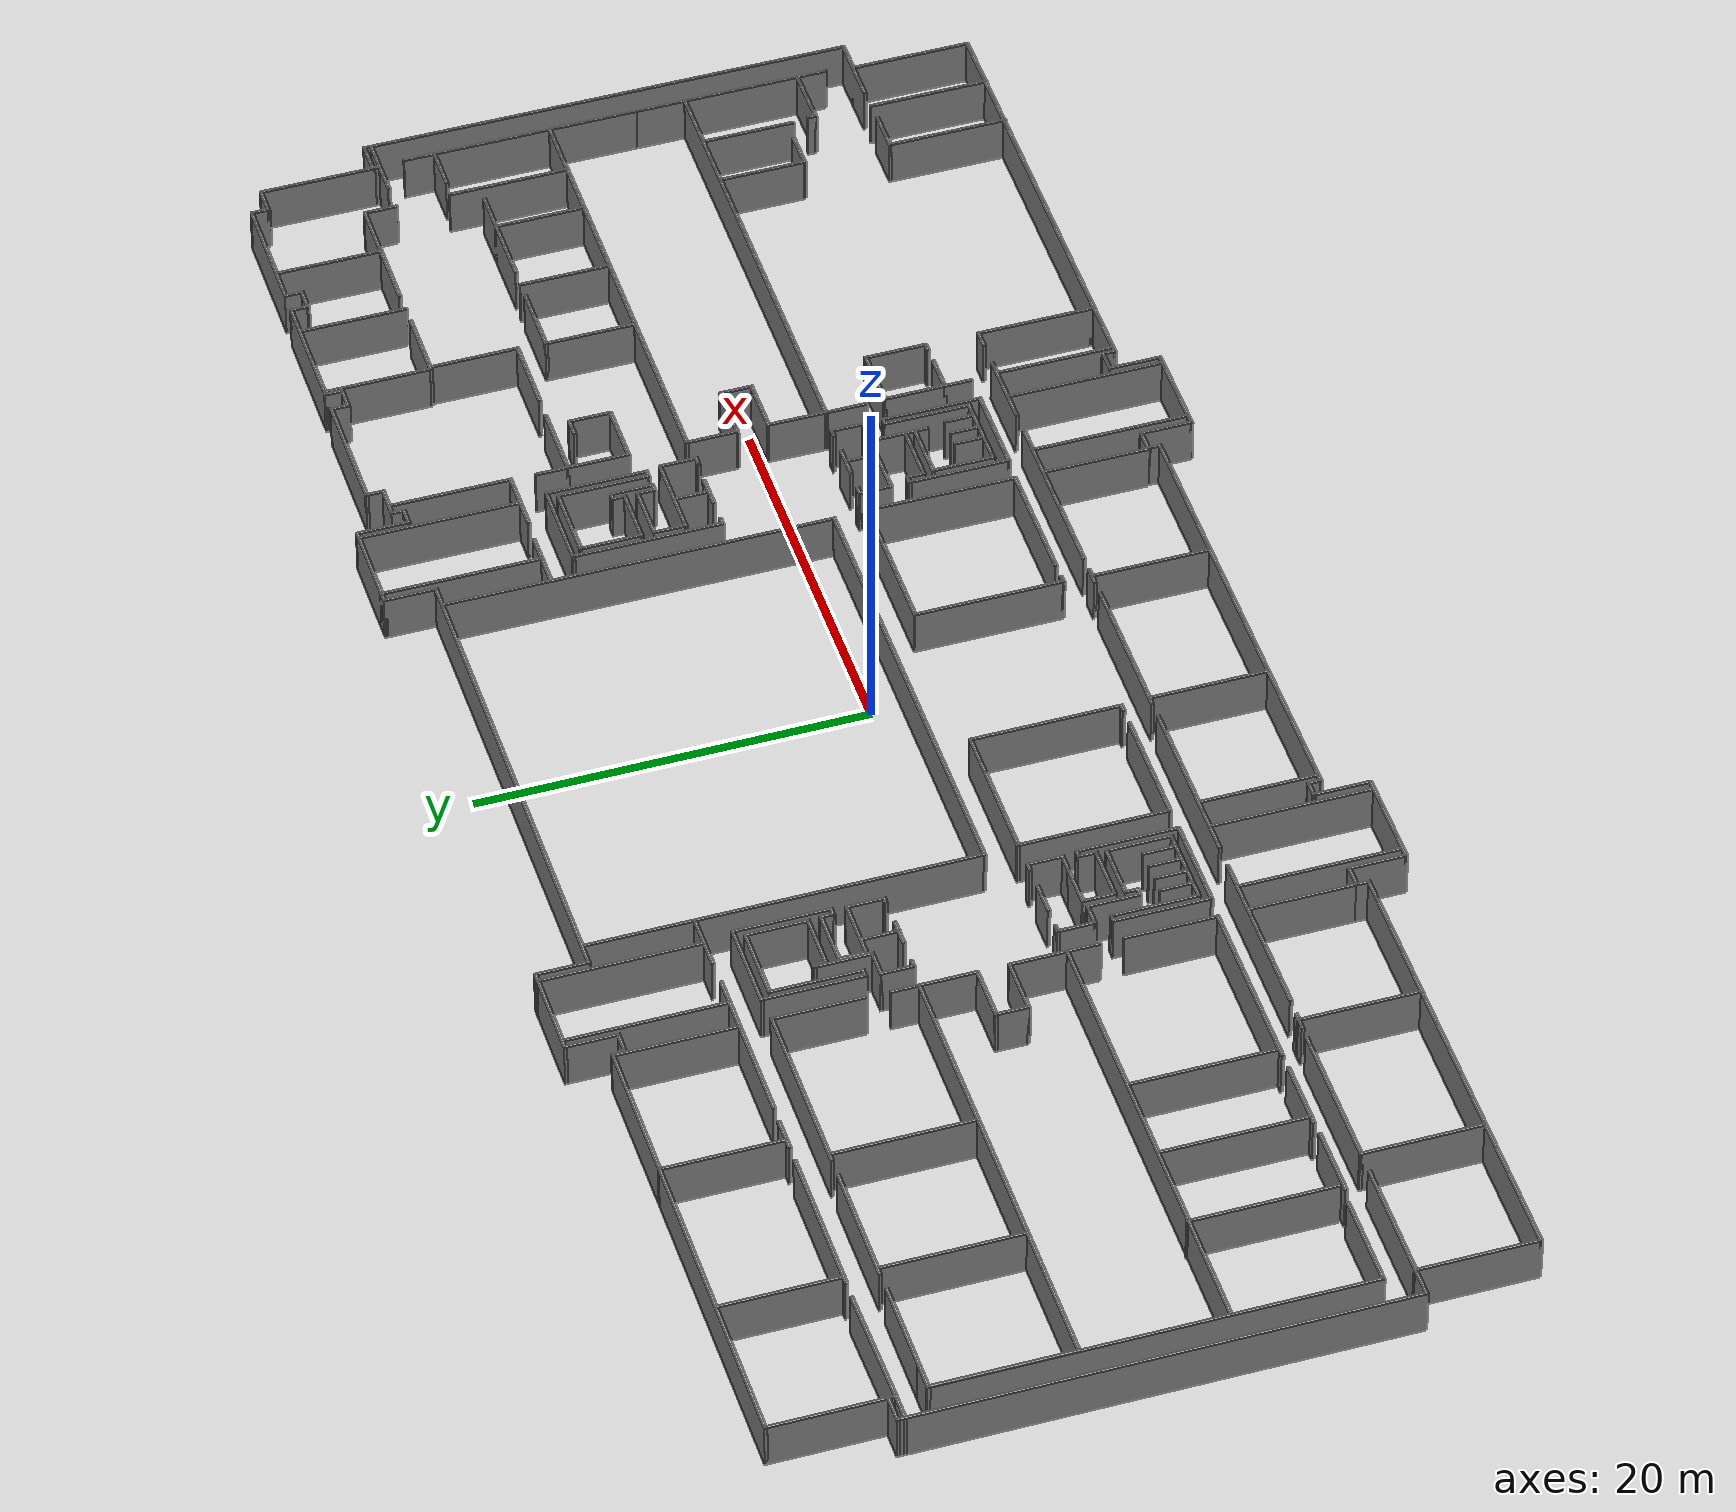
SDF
<sdf version="1.7">
 <world name="default">
  <light name="sun" type="directional">
   <pose>0 0 10 0 -0 0</pose>
   <diffuse>0.8 0.8 0.8 1</diffuse>
   <specular>0.2 0.2 0.2 1</specular>
   <attenuation>
    <range>1000</range>
    <constant>0.9</constant>
    <linear>0.01</linear>
    <quadratic>0.001</quadratic>
   </attenuation>
   <direction>-0.5 0.1 -0.9</direction>
   <spot><inner_angle>0</inner_angle><outer_angle>0</outer_angle><falloff>0</falloff></spot>
  </light>
  <model name="ground_plane">
   <static>1</static>
   <link name="link">
    <collision name="collision">
     <geometry><plane><normal>0 0 1</normal><size>100 100</size></plane></geometry>
     <surface>
      <contact><collide_bitmask>65535</collide_bitmask></contact>
      <friction><ode><mu>100</mu><mu2>50</mu2></ode></friction>
     </surface>
    </collision>
    <visual name="visual">
     <cast_shadows>0</cast_shadows>
     <geometry><plane><normal>0 0 1</normal><size>100 100</size></plane></geometry>
     <material>
      <script><uri>file://media/materials/scripts/gazebo.material</uri><name>Gazebo/Grey</name></script>
     </material>
    </visual>
   </link>
  </model>
  <gravity>0 0 -9.8</gravity>
  <magnetic_field>6e-06 2.3e-05 -4.2e-05</magnetic_field>
  <atmosphere type="adiabatic"/>
  <physics type="ode">
   <max_step_size>0.001</max_step_size>
   <real_time_factor>1</real_time_factor>
   <real_time_update_rate>1000</real_time_update_rate>
  </physics>
  <scene><ambient>0.4 0.4 0.4 1</ambient><background>0.7 0.7 0.7 1</background><shadows>1</shadows></scene>
  <spherical_coordinates>
   <surface_model>EARTH_WGS84</surface_model>
   <latitude_deg>0</latitude_deg>
   <longitude_deg>0</longitude_deg>
   <elevation>0</elevation>
   <heading_deg>0</heading_deg>
  </spherical_coordinates>
  <model name="minerva">
   <pose>-0.765751 0.164905 0 0 -0 0</pose>
   <link name="Wall_0">
    <collision name="Wall_0_Collision">
     <geometry><box><size>26.25 0.15 2.5</size></box></geometry>
     <pose>0 0 1.25 0 -0 0</pose>
    </collision>
    <visual name="Wall_0_Visual">
     <pose>0 0 1.25 0 -0 0</pose>
     <geometry><box><size>26.25 0.15 2.5</size></box></geometry>
     <material>
      <script><uri>file://media/materials/scripts/gazebo.material</uri><name>Gazebo/Grey</name></script>
      <ambient>1 1 1 1</ambient>
     </material>
     <meta><layer>0</layer></meta>
    </visual>
    <pose>-0.05 18.1608 0 0 -0 0</pose>
   </link>
   <link name="Wall_1">
    <collision name="Wall_1_Collision">
     <geometry><box><size>2.75 0.15 2.5</size></box></geometry>
     <pose>0 0 1.25 0 -0 0</pose>
    </collision>
    <visual name="Wall_1_Visual">
     <pose>0 0 1.25 0 -0 0</pose>
     <geometry><box><size>2.75 0.15 2.5</size></box></geometry>
     <material>
      <script><uri>file://media/materials/scripts/gazebo.material</uri><name>Gazebo/Grey</name></script>
      <ambient>1 1 1 1</ambient>
     </material>
     <meta><layer>0</layer></meta>
    </visual>
    <pose>13 19.4608 0 0 -0 1.5708</pose>
   </link>
   <link name="Wall_10">
    <collision name="Wall_10_Collision">
     <geometry><box><size>0.75 0.15 2.5</size></box></geometry>
     <pose>0 0 1.25 0 -0 0</pose>
    </collision>
    <visual name="Wall_10_Visual">
     <pose>0 0 1.25 0 -0 0</pose>
     <geometry><box><size>0.75 0.15 2.5</size></box></geometry>
     <material>
      <script><uri>file://media/materials/scripts/gazebo.material</uri><name>Gazebo/Grey</name></script>
      <ambient>1 1 1 1</ambient>
     </material>
     <meta><layer>0</layer></meta>
    </visual>
    <pose>-19.05 18.4608 0 0 -0 1.5708</pose>
   </link>
   <link name="Wall_102">
    <collision name="Wall_102_Collision">
     <geometry><box><size>5.5 0.15 2.5</size></box></geometry>
     <pose>0 0 1.25 0 -0 0</pose>
    </collision>
    <visual name="Wall_102_Visual">
     <pose>0 0 1.25 0 -0 0</pose>
     <geometry><box><size>5.5 0.15 2.5</size></box></geometry>
     <material>
      <script><uri>file://media/materials/scripts/gazebo.material</uri><name>Gazebo/Grey</name></script>
      <ambient>1 1 1 1</ambient>
     </material>
     <meta><layer>0</layer></meta>
    </visual>
    <pose>11.8632 -15.1957 0 0 -0 -1.5708</pose>
   </link>
   <link name="Wall_104">
    <collision name="Wall_104_Collision">
     <geometry><box><size>4 0.15 2.5</size></box></geometry>
     <pose>0 0 1.25 0 -0 0</pose>
    </collision>
    <visual name="Wall_104_Visual">
     <pose>0 0 1.25 0 -0 0</pose>
     <geometry><box><size>4 0.15 2.5</size></box></geometry>
     <material>
      <script><uri>file://media/materials/scripts/gazebo.material</uri><name>Gazebo/Grey</name></script>
      <ambient>1 1 1 1</ambient>
     </material>
     <meta><layer>0</layer></meta>
    </visual>
    <pose>18.0466 -12.4902 0 0 -0 0</pose>
   </link>
   <link name="Wall_106">
    <collision name="Wall_106_Collision">
     <geometry><box><size>8 0.15 2.5</size></box></geometry>
     <pose>0 0 1.25 0 -0 0</pose>
    </collision>
    <visual name="Wall_106_Visual">
     <pose>0 0 1.25 0 -0 0</pose>
     <geometry><box><size>8 0.15 2.5</size></box></geometry>
     <material>
      <script><uri>file://media/materials/scripts/gazebo.material</uri><name>Gazebo/Grey</name></script>
      <ambient>1 1 1 1</ambient>
     </material>
     <meta><layer>0</layer></meta>
    </visual>
    <pose>13.521 -16.4913 0 0 -0 -1.5708</pose>
   </link>
   <link name="Wall_110">
    <collision name="Wall_110_Collision">
     <geometry><box><size>8 0.15 2.5</size></box></geometry>
     <pose>0 0 1.25 0 -0 0</pose>
    </collision>
    <visual name="Wall_110_Visual">
     <pose>0 0 1.25 0 -0 0</pose>
     <geometry><box><size>8 0.15 2.5</size></box></geometry>
     <material>
      <script><uri>file://media/materials/scripts/gazebo.material</uri><name>Gazebo/Grey</name></script>
      <ambient>1 1 1 1</ambient>
     </material>
     <meta><layer>0</layer></meta>
    </visual>
    <pose>17.4752 -16.5217 0 0 -0 -1.5708</pose>
   </link>
   <link name="Wall_112">
    <collision name="Wall_112_Collision">
     <geometry><box><size>6 0.15 2.5</size></box></geometry>
     <pose>0 0 1.25 0 -0 0</pose>
    </collision>
    <visual name="Wall_112_Visual">
     <pose>0 0 1.25 0 -0 0</pose>
     <geometry><box><size>6 0.15 2.5</size></box></geometry>
     <material>
      <script><uri>file://media/materials/scripts/gazebo.material</uri><name>Gazebo/Grey</name></script>
      <ambient>1 1 1 1</ambient>
     </material>
     <meta><layer>0</layer></meta>
    </visual>
    <pose>19.2547 -15.4913 0 0 -0 -1.5708</pose>
   </link>
   <link name="Wall_114">
    <collision name="Wall_114_Collision">
     <geometry><box><size>1.01534 0.15 2.5</size></box></geometry>
     <pose>0 0 1.25 0 -0 0</pose>
    </collision>
    <visual name="Wall_114_Visual">
     <pose>0 0 1.25 0 -0 0</pose>
     <geometry><box><size>1.01534 0.15 2.5</size></box></geometry>
     <material>
      <script><uri>file://media/materials/scripts/gazebo.material</uri><name>Gazebo/Grey</name></script>
      <ambient>1 1 1 1</ambient>
     </material>
     <meta><layer>0</layer></meta>
    </visual>
    <pose>21.8013 -12.4978 0 0 -0 -0.017576</pose>
   </link>
   <link name="Wall_115">
    <collision name="Wall_115_Collision">
     <geometry><box><size>6 0.15 2.5</size></box></geometry>
     <pose>0 0 1.25 0 -0 0</pose>
    </collision>
    <visual name="Wall_115_Visual">
     <pose>0 0 1.25 0 -0 0</pose>
     <geometry><box><size>6 0.15 2.5</size></box></geometry>
     <material>
      <script><uri>file://media/materials/scripts/gazebo.material</uri><name>Gazebo/Grey</name></script>
      <ambient>1 1 1 1</ambient>
     </material>
     <meta><layer>0</layer></meta>
    </visual>
    <pose>22.2339 -15.4457 0 0 -0 -1.5708</pose>
   </link>
   <link name="Wall_117">
    <collision name="Wall_117_Collision">
     <geometry><box><size>0.25 0.15 2.5</size></box></geometry>
     <pose>0 0 1.25 0 -0 0</pose>
    </collision>
    <visual name="Wall_117_Visual">
     <pose>0 0 1.25 0 -0 0</pose>
     <geometry><box><size>0.25 0.15 2.5</size></box></geometry>
     <material>
      <script><uri>file://media/materials/scripts/gazebo.material</uri><name>Gazebo/Grey</name></script>
      <ambient>1 1 1 1</ambient>
     </material>
     <meta><layer>0</layer></meta>
    </visual>
    <pose>22.2339 -18.4207 0 0 -0 -1.5708</pose>
   </link>
   <link name="Wall_119">
    <collision name="Wall_119_Collision">
     <geometry><box><size>12.25 0.15 2.5</size></box></geometry>
     <pose>0 0 1.25 0 -0 0</pose>
    </collision>
    <visual name="Wall_119_Visual">
     <pose>0 0 1.25 0 -0 0</pose>
     <geometry><box><size>12.25 0.15 2.5</size></box></geometry>
     <material>
      <script><uri>file://media/materials/scripts/gazebo.material</uri><name>Gazebo/Grey</name></script>
      <ambient>1 1 1 1</ambient>
     </material>
     <meta><layer>0</layer></meta>
    </visual>
    <pose>43.02 5.16842 0 0 -0 -1.5708</pose>
   </link>
   <link name="Wall_121">
    <collision name="Wall_121_Collision">
     <geometry><box><size>10.25 0.15 2.5</size></box></geometry>
     <pose>0 0 1.25 0 -0 0</pose>
    </collision>
    <visual name="Wall_121_Visual">
     <pose>0 0 1.25 0 -0 0</pose>
     <geometry><box><size>10.25 0.15 2.5</size></box></geometry>
     <material>
      <script><uri>file://media/materials/scripts/gazebo.material</uri><name>Gazebo/Grey</name></script>
      <ambient>1 1 1 1</ambient>
     </material>
     <meta><layer>0</layer></meta>
    </visual>
    <pose>43.02 -5.93158 0 0 -0 -1.5708</pose>
   </link>
   <link name="Wall_123">
    <collision name="Wall_123_Collision">
     <geometry><box><size>3.25 0.15 2.5</size></box></geometry>
     <pose>0 0 1.25 0 -0 0</pose>
    </collision>
    <visual name="Wall_123_Visual">
     <pose>0 0 1.25 0 -0 0</pose>
     <geometry><box><size>3.25 0.15 2.5</size></box></geometry>
     <material>
      <script><uri>file://media/materials/scripts/gazebo.material</uri><name>Gazebo/Grey</name></script>
      <ambient>1 1 1 1</ambient>
     </material>
     <meta><layer>0</layer></meta>
    </visual>
    <pose>41.4931 -9.52973 0 0 -0 3.14159</pose>
   </link>
   <link name="Wall_124">
    <collision name="Wall_124_Collision">
     <geometry><box><size>0.5 0.15 2.5</size></box></geometry>
     <pose>0 0 1.25 0 -0 0</pose>
    </collision>
    <visual name="Wall_124_Visual">
     <pose>0 0 1.25 0 -0 0</pose>
     <geometry><box><size>0.5 0.15 2.5</size></box></geometry>
     <material>
      <script><uri>file://media/materials/scripts/gazebo.material</uri><name>Gazebo/Grey</name></script>
      <ambient>1 1 1 1</ambient>
     </material>
     <meta><layer>0</layer></meta>
    </visual>
    <pose>39.9431 -9.35473 0 0 -0 1.5708</pose>
   </link>
   <link name="Wall_126">
    <collision name="Wall_126_Collision">
     <geometry><box><size>4.75 0.15 2.5</size></box></geometry>
     <pose>0 0 1.25 0 -0 0</pose>
    </collision>
    <visual name="Wall_126_Visual">
     <pose>0 0 1.25 0 -0 0</pose>
     <geometry><box><size>4.75 0.15 2.5</size></box></geometry>
     <material>
      <script><uri>file://media/materials/scripts/gazebo.material</uri><name>Gazebo/Grey</name></script>
      <ambient>1 1 1 1</ambient>
     </material>
     <meta><layer>0</layer></meta>
    </visual>
    <pose>39.8077 -5.97793 0 0 -0 -1.5708</pose>
   </link>
   <link name="Wall_128">
    <collision name="Wall_128_Collision">
     <geometry><box><size>4.5 0.15 2.5</size></box></geometry>
     <pose>0 0 1.25 0 -0 0</pose>
    </collision>
    <visual name="Wall_128_Visual">
     <pose>0 0 1.25 0 -0 0</pose>
     <geometry><box><size>4.5 0.15 2.5</size></box></geometry>
     <material>
      <script><uri>file://media/materials/scripts/gazebo.material</uri><name>Gazebo/Grey</name></script>
      <ambient>1 1 1 1</ambient>
     </material>
     <meta><layer>0</layer></meta>
    </visual>
    <pose>36.8268 -5.8073 0 0 -0 -1.5708</pose>
   </link>
   <link name="Wall_129">
    <collision name="Wall_129_Collision">
     <geometry><box><size>2 0.15 2.5</size></box></geometry>
     <pose>0 0 1.25 0 -0 0</pose>
    </collision>
    <visual name="Wall_129_Visual">
     <pose>0 0 1.25 0 -0 0</pose>
     <geometry><box><size>2 0.15 2.5</size></box></geometry>
     <material>
      <script><uri>file://media/materials/scripts/gazebo.material</uri><name>Gazebo/Grey</name></script>
      <ambient>1 1 1 1</ambient>
     </material>
     <meta><layer>0</layer></meta>
    </visual>
    <pose>37.7518 -7.9823 0 0 -0 0</pose>
   </link>
   <link name="Wall_13">
    <collision name="Wall_13_Collision">
     <geometry><box><size>24.25 0.15 2.5</size></box></geometry>
     <pose>0 0 1.25 0 -0 0</pose>
    </collision>
    <visual name="Wall_13_Visual">
     <pose>0 0 1.25 0 -0 0</pose>
     <geometry><box><size>24.25 0.15 2.5</size></box></geometry>
     <material>
      <script><uri>file://media/materials/scripts/gazebo.material</uri><name>Gazebo/Grey</name></script>
      <ambient>1 1 1 1</ambient>
     </material>
     <meta><layer>0</layer></meta>
    </visual>
    <pose>-31.1 18.7608 0 0 -0 3.14159</pose>
   </link>
   <link name="Wall_131">
    <collision name="Wall_131_Collision">
     <geometry><box><size>24 0.15 2.5</size></box></geometry>
     <pose>0 0 1.25 0 -0 0</pose>
    </collision>
    <visual name="Wall_131_Visual">
     <pose>0 0 1.25 0 -0 0</pose>
     <geometry><box><size>24 0.15 2.5</size></box></geometry>
     <material>
      <script><uri>file://media/materials/scripts/gazebo.material</uri><name>Gazebo/Grey</name></script>
      <ambient>1 1 1 1</ambient>
     </material>
     <meta><layer>0</layer></meta>
    </visual>
    <pose>31.0157 -3.55626 0 0 -0 3.14159</pose>
   </link>
   <link name="Wall_133">
    <collision name="Wall_133_Collision">
     <geometry><box><size>2.25 0.15 2.5</size></box></geometry>
     <pose>0 0 1.25 0 -0 0</pose>
    </collision>
    <visual name="Wall_133_Visual">
     <pose>0 0 1.25 0 -0 0</pose>
     <geometry><box><size>2.25 0.15 2.5</size></box></geometry>
     <material>
      <script><uri>file://media/materials/scripts/gazebo.material</uri><name>Gazebo/Grey</name></script>
      <ambient>1 1 1 1</ambient>
     </material>
     <meta><layer>0</layer></meta>
    </visual>
    <pose>19.0907 -4.60626 0 0 -0 -1.5708</pose>
   </link>
   <link name="Wall_135">
    <collision name="Wall_135_Collision">
     <geometry><box><size>24 0.15 2.5</size></box></geometry>
     <pose>0 0 1.25 0 -0 0</pose>
    </collision>
    <visual name="Wall_135_Visual">
     <pose>0 0 1.25 0 -0 0</pose>
     <geometry><box><size>24 0.15 2.5</size></box></geometry>
     <material>
      <script><uri>file://media/materials/scripts/gazebo.material</uri><name>Gazebo/Grey</name></script>
      <ambient>1 1 1 1</ambient>
     </material>
     <meta><layer>0</layer></meta>
    </visual>
    <pose>31.0488 3.59185 0 0 -0 0</pose>
   </link>
   <link name="Wall_137">
    <collision name="Wall_137_Collision">
     <geometry><box><size>2.75 0.15 2.5</size></box></geometry>
     <pose>0 0 1.25 0 -0 0</pose>
    </collision>
    <visual name="Wall_137_Visual">
     <pose>0 0 1.25 0 -0 0</pose>
     <geometry><box><size>2.75 0.15 2.5</size></box></geometry>
     <material>
      <script><uri>file://media/materials/scripts/gazebo.material</uri><name>Gazebo/Grey</name></script>
      <ambient>1 1 1 1</ambient>
     </material>
     <meta><layer>0</layer></meta>
    </visual>
    <pose>19.1238 2.29185 0 0 -0 -1.5708</pose>
   </link>
   <link name="Wall_138">
    <collision name="Wall_138_Collision">
     <geometry><box><size>3 0.15 2.5</size></box></geometry>
     <pose>0 0 1.25 0 -0 0</pose>
    </collision>
    <visual name="Wall_138_Visual">
     <pose>0 0 1.25 0 -0 0</pose>
     <geometry><box><size>3 0.15 2.5</size></box></geometry>
     <material>
      <script><uri>file://media/materials/scripts/gazebo.material</uri><name>Gazebo/Grey</name></script>
      <ambient>1 1 1 1</ambient>
     </material>
     <meta><layer>0</layer></meta>
    </visual>
    <pose>20.5488 0.991855 0 0 -0 0</pose>
   </link>
   <link name="Wall_139">
    <collision name="Wall_139_Collision">
     <geometry><box><size>1.75 0.15 2.5</size></box></geometry>
     <pose>0 0 1.25 0 -0 0</pose>
    </collision>
    <visual name="Wall_139_Visual">
     <pose>0 0 1.25 0 -0 0</pose>
     <geometry><box><size>1.75 0.15 2.5</size></box></geometry>
     <material>
      <script><uri>file://media/materials/scripts/gazebo.material</uri><name>Gazebo/Grey</name></script>
      <ambient>1 1 1 1</ambient>
     </material>
     <meta><layer>0</layer></meta>
    </visual>
    <pose>21.9738 0.191855 0 0 -0 -1.5708</pose>
   </link>
   <link name="Wall_14">
    <collision name="Wall_14_Collision">
     <geometry><box><size>6 0.15 2.5</size></box></geometry>
     <pose>0 0 1.25 0 -0 0</pose>
    </collision>
    <visual name="Wall_14_Visual">
     <pose>0 0 1.25 0 -0 0</pose>
     <geometry><box><size>6 0.15 2.5</size></box></geometry>
     <material>
      <script><uri>file://media/materials/scripts/gazebo.material</uri><name>Gazebo/Grey</name></script>
      <ambient>1 1 1 1</ambient>
     </material>
     <meta><layer>0</layer></meta>
    </visual>
    <pose>-43.15 15.8358 0 0 -0 -1.5708</pose>
   </link>
   <link name="Wall_140">
    <collision name="Wall_140_Collision">
     <geometry><box><size>3 0.15 2.5</size></box></geometry>
     <pose>0 0 1.25 0 -0 0</pose>
    </collision>
    <visual name="Wall_140_Visual">
     <pose>0 0 1.25 0 -0 0</pose>
     <geometry><box><size>3 0.15 2.5</size></box></geometry>
     <material>
      <script><uri>file://media/materials/scripts/gazebo.material</uri><name>Gazebo/Grey</name></script>
      <ambient>1 1 1 1</ambient>
     </material>
     <meta><layer>0</layer></meta>
    </visual>
    <pose>20.5488 -0.608145 0 0 -0 3.14159</pose>
   </link>
   <link name="Wall_142">
    <collision name="Wall_142_Collision">
     <geometry><box><size>5.5 0.15 2.5</size></box></geometry>
     <pose>0 0 1.25 0 -0 0</pose>
    </collision>
    <visual name="Wall_142_Visual">
     <pose>0 0 1.25 0 -0 0</pose>
     <geometry><box><size>5.5 0.15 2.5</size></box></geometry>
     <material>
      <script><uri>file://media/materials/scripts/gazebo.material</uri><name>Gazebo/Grey</name></script>
      <ambient>1 1 1 1</ambient>
     </material>
     <meta><layer>0</layer></meta>
    </visual>
    <pose>32.4923 16.8369 0 0 -0 1.5708</pose>
   </link>
   <link name="Wall_144">
    <collision name="Wall_144_Collision">
     <geometry><box><size>6.5 0.15 2.5</size></box></geometry>
     <pose>0 0 1.25 0 -0 0</pose>
    </collision>
    <visual name="Wall_144_Visual">
     <pose>0 0 1.25 0 -0 0</pose>
     <geometry><box><size>6.5 0.15 2.5</size></box></geometry>
     <material>
      <script><uri>file://media/materials/scripts/gazebo.material</uri><name>Gazebo/Grey</name></script>
      <ambient>1 1 1 1</ambient>
     </material>
     <meta><layer>0</layer></meta>
    </visual>
    <pose>36.6783 14.1924 0 0 -0 3.14159</pose>
   </link>
   <link name="Wall_146">
    <collision name="Wall_146_Collision">
     <geometry><box><size>3.75 0.15 2.5</size></box></geometry>
     <pose>0 0 1.25 0 -0 0</pose>
    </collision>
    <visual name="Wall_146_Visual">
     <pose>0 0 1.25 0 -0 0</pose>
     <geometry><box><size>3.75 0.15 2.5</size></box></geometry>
     <material>
      <script><uri>file://media/materials/scripts/gazebo.material</uri><name>Gazebo/Grey</name></script>
      <ambient>1 1 1 1</ambient>
     </material>
     <meta><layer>0</layer></meta>
    </visual>
    <pose>29.7341 14.1619 0 0 -0 3.14159</pose>
   </link>
   <link name="Wall_147">
    <collision name="Wall_147_Collision">
     <geometry><box><size>5.5 0.15 2.5</size></box></geometry>
     <pose>0 0 1.25 0 -0 0</pose>
    </collision>
    <visual name="Wall_147_Visual">
     <pose>0 0 1.25 0 -0 0</pose>
     <geometry><box><size>5.5 0.15 2.5</size></box></geometry>
     <material>
      <script><uri>file://media/materials/scripts/gazebo.material</uri><name>Gazebo/Grey</name></script>
      <ambient>1 1 1 1</ambient>
     </material>
     <meta><layer>0</layer></meta>
    </visual>
    <pose>27.9341 16.8369 0 0 -0 1.5708</pose>
   </link>
   <link name="Wall_149">
    <collision name="Wall_149_Collision">
     <geometry><box><size>5.5 0.15 2.5</size></box></geometry>
     <pose>0 0 1.25 0 -0 0</pose>
    </collision>
    <visual name="Wall_149_Visual">
     <pose>0 0 1.25 0 -0 0</pose>
     <geometry><box><size>5.5 0.15 2.5</size></box></geometry>
     <material>
      <script><uri>file://media/materials/scripts/gazebo.material</uri><name>Gazebo/Grey</name></script>
      <ambient>1 1 1 1</ambient>
     </material>
     <meta><layer>0</layer></meta>
    </visual>
    <pose>36.9028 16.8674 0 0 -0 1.5708</pose>
   </link>
   <link name="Wall_15">
    <collision name="Wall_15_Collision">
     <geometry><box><size>1.5 0.15 2.5</size></box></geometry>
     <pose>0 0 1.25 0 -0 0</pose>
    </collision>
    <visual name="Wall_15_Visual">
     <pose>0 0 1.25 0 -0 0</pose>
     <geometry><box><size>1.5 0.15 2.5</size></box></geometry>
     <material>
      <script><uri>file://media/materials/scripts/gazebo.material</uri><name>Gazebo/Grey</name></script>
      <ambient>1 1 1 1</ambient>
     </material>
     <meta><layer>0</layer></meta>
    </visual>
    <pose>-43.825 12.9108 0 0 -0 3.14159</pose>
   </link>
   <link name="Wall_151">
    <collision name="Wall_151_Collision">
     <geometry><box><size>1.75 0.15 2.5</size></box></geometry>
     <pose>0 0 1.25 0 -0 0</pose>
    </collision>
    <visual name="Wall_151_Visual">
     <pose>0 0 1.25 0 -0 0</pose>
     <geometry><box><size>1.75 0.15 2.5</size></box></geometry>
     <material>
      <script><uri>file://media/materials/scripts/gazebo.material</uri><name>Gazebo/Grey</name></script>
      <ambient>1 1 1 1</ambient>
     </material>
     <meta><layer>0</layer></meta>
    </visual>
    <pose>39.8533 13.3924 0 0 -0 -1.5708</pose>
   </link>
   <link name="Wall_157">
    <collision name="Wall_157_Collision">
     <geometry><box><size>3.25 0.15 2.5</size></box></geometry>
     <pose>0 0 1.25 0 -0 0</pose>
    </collision>
    <visual name="Wall_157_Visual">
     <pose>0 0 1.25 0 -0 0</pose>
     <geometry><box><size>3.25 0.15 2.5</size></box></geometry>
     <material>
      <script><uri>file://media/materials/scripts/gazebo.material</uri><name>Gazebo/Grey</name></script>
      <ambient>1 1 1 1</ambient>
     </material>
     <meta><layer>0</layer></meta>
    </visual>
    <pose>42.8075 12.558 0 0 -0 0</pose>
   </link>
   <link name="Wall_159">
    <collision name="Wall_159_Collision">
     <geometry><box><size>0.5 0.15 2.5</size></box></geometry>
     <pose>0 0 1.25 0 -0 0</pose>
    </collision>
    <visual name="Wall_159_Visual">
     <pose>0 0 1.25 0 -0 0</pose>
     <geometry><box><size>0.5 0.15 2.5</size></box></geometry>
     <material>
      <script><uri>file://media/materials/scripts/gazebo.material</uri><name>Gazebo/Grey</name></script>
      <ambient>1 1 1 1</ambient>
     </material>
     <meta><layer>0</layer></meta>
    </visual>
    <pose>42.9 12.7358 0 0 -0 -1.5708</pose>
   </link>
   <link name="Wall_161">
    <collision name="Wall_161_Collision">
     <geometry><box><size>2.25 0.15 2.5</size></box></geometry>
     <pose>0 0 1.25 0 -0 0</pose>
    </collision>
    <visual name="Wall_161_Visual">
     <pose>0 0 1.25 0 -0 0</pose>
     <geometry><box><size>2.25 0.15 2.5</size></box></geometry>
     <material>
      <script><uri>file://media/materials/scripts/gazebo.material</uri><name>Gazebo/Grey</name></script>
      <ambient>1 1 1 1</ambient>
     </material>
     <meta><layer>0</layer></meta>
    </visual>
    <pose>41.8443 9.66213 0 0 -0 0</pose>
   </link>
   <link name="Wall_165">
    <collision name="Wall_165_Collision">
     <geometry><box><size>6.25 0.15 2.5</size></box></geometry>
     <pose>0 0 1.25 0 -0 0</pose>
    </collision>
    <visual name="Wall_165_Visual">
     <pose>0 0 1.25 0 -0 0</pose>
     <geometry><box><size>6.25 0.15 2.5</size></box></geometry>
     <material>
      <script><uri>file://media/materials/scripts/gazebo.material</uri><name>Gazebo/Grey</name></script>
      <ambient>1 1 1 1</ambient>
     </material>
     <meta><layer>0</layer></meta>
    </visual>
    <pose>39.8814 6.67712 0 0 -0 -1.5708</pose>
   </link>
   <link name="Wall_167">
    <collision name="Wall_167_Collision">
     <geometry><box><size>3.75 0.15 2.5</size></box></geometry>
     <pose>0 0 1.25 0 -0 0</pose>
    </collision>
    <visual name="Wall_167_Visual">
     <pose>0 0 1.25 0 -0 0</pose>
     <geometry><box><size>3.75 0.15 2.5</size></box></geometry>
     <material>
      <script><uri>file://media/materials/scripts/gazebo.material</uri><name>Gazebo/Grey</name></script>
      <ambient>1 1 1 1</ambient>
     </material>
     <meta><layer>0</layer></meta>
    </visual>
    <pose>29.7921 8.20624 0 0 -0 0</pose>
   </link>
   <link name="Wall_169">
    <collision name="Wall_169_Collision">
     <geometry><box><size>5.75 0.15 2.5</size></box></geometry>
     <pose>0 0 1.25 0 -0 0</pose>
    </collision>
    <visual name="Wall_169_Visual">
     <pose>0 0 1.25 0 -0 0</pose>
     <geometry><box><size>5.75 0.15 2.5</size></box></geometry>
     <material>
      <script><uri>file://media/materials/scripts/gazebo.material</uri><name>Gazebo/Grey</name></script>
      <ambient>1 1 1 1</ambient>
     </material>
     <meta><layer>0</layer></meta>
    </visual>
    <pose>36.2143 8.17979 0 0 -0 0</pose>
   </link>
   <link name="Wall_17">
    <collision name="Wall_17_Collision">
     <geometry><box><size>25.5 0.15 2.5</size></box></geometry>
     <pose>0 0 1.25 0 -0 0</pose>
    </collision>
    <visual name="Wall_17_Visual">
     <pose>0 0 1.25 0 -0 0</pose>
     <geometry><box><size>25.5 0.15 2.5</size></box></geometry>
     <material>
      <script><uri>file://media/materials/scripts/gazebo.material</uri><name>Gazebo/Grey</name></script>
      <ambient>1 1 1 1</ambient>
     </material>
     <meta><layer>0</layer></meta>
    </visual>
    <pose>-44.5 0.235782 0 0 -0 -1.5708</pose>
   </link>
   <link name="Wall_171">
    <collision name="Wall_171_Collision">
     <geometry><box><size>4.75 0.15 2.5</size></box></geometry>
     <pose>0 0 1.25 0 -0 0</pose>
    </collision>
    <visual name="Wall_171_Visual">
     <pose>0 0 1.25 0 -0 0</pose>
     <geometry><box><size>4.75 0.15 2.5</size></box></geometry>
     <material>
      <script><uri>file://media/materials/scripts/gazebo.material</uri><name>Gazebo/Grey</name></script>
      <ambient>1 1 1 1</ambient>
     </material>
     <meta><layer>0</layer></meta>
    </visual>
    <pose>36.919 5.87979 0 0 -0 -1.5708</pose>
   </link>
   <link name="Wall_173">
    <collision name="Wall_173_Collision">
     <geometry><box><size>4.75 0.15 2.5</size></box></geometry>
     <pose>0 0 1.25 0 -0 0</pose>
    </collision>
    <visual name="Wall_173_Visual">
     <pose>0 0 1.25 0 -0 0</pose>
     <geometry><box><size>4.75 0.15 2.5</size></box></geometry>
     <material>
      <script><uri>file://media/materials/scripts/gazebo.material</uri><name>Gazebo/Grey</name></script>
      <ambient>1 1 1 1</ambient>
     </material>
     <meta><layer>0</layer></meta>
    </visual>
    <pose>32.4621 5.89302 0 0 -0 -1.5708</pose>
   </link>
   <link name="Wall_175">
    <collision name="Wall_175_Collision">
     <geometry><box><size>4.75 0.15 2.5</size></box></geometry>
     <pose>0 0 1.25 0 -0 0</pose>
    </collision>
    <visual name="Wall_175_Visual">
     <pose>0 0 1.25 0 -0 0</pose>
     <geometry><box><size>4.75 0.15 2.5</size></box></geometry>
     <material>
      <script><uri>file://media/materials/scripts/gazebo.material</uri><name>Gazebo/Grey</name></script>
      <ambient>1 1 1 1</ambient>
     </material>
     <meta><layer>0</layer></meta>
    </visual>
    <pose>27.9921 5.90624 0 0 -0 -1.5708</pose>
   </link>
   <link name="Wall_177">
    <collision name="Wall_177_Collision">
     <geometry><box><size>3.0983 0.15 2.5</size></box></geometry>
     <pose>0 0 1.25 0 -0 0</pose>
    </collision>
    <visual name="Wall_177_Visual">
     <pose>0 0 1.25 0 -0 0</pose>
     <geometry><box><size>3.0983 0.15 2.5</size></box></geometry>
     <material>
      <script><uri>file://media/materials/scripts/gazebo.material</uri><name>Gazebo/Grey</name></script>
      <ambient>1 1 1 1</ambient>
     </material>
     <meta><layer>0</layer></meta>
    </visual>
    <pose>19.1072 -2.0822 0 0 -0 -1.58202</pose>
   </link>
   <link name="Wall_179">
    <collision name="Wall_179_Collision">
     <geometry><box><size>3.25 0.15 2.5</size></box></geometry>
     <pose>0 0 1.25 0 -0 0</pose>
    </collision>
    <visual name="Wall_179_Visual">
     <pose>0 0 1.25 0 -0 0</pose>
     <geometry><box><size>3.25 0.15 2.5</size></box></geometry>
     <material>
      <script><uri>file://media/materials/scripts/gazebo.material</uri><name>Gazebo/Grey</name></script>
      <ambient>1 1 1 1</ambient>
     </material>
     <meta><layer>0</layer></meta>
    </visual>
    <pose>20.6923 -6.63787 0 0 -0 0</pose>
   </link>
   <link name="Wall_18">
    <collision name="Wall_18_Collision">
     <geometry><box><size>8 0.15 2.5</size></box></geometry>
     <pose>0 0 1.25 0 -0 0</pose>
    </collision>
    <visual name="Wall_18_Visual">
     <pose>0 0 1.25 0 -0 0</pose>
     <geometry><box><size>8 0.15 2.5</size></box></geometry>
     <material>
      <script><uri>file://media/materials/scripts/gazebo.material</uri><name>Gazebo/Grey</name></script>
      <ambient>1 1 1 1</ambient>
     </material>
     <meta><layer>0</layer></meta>
    </visual>
    <pose>-40.575 -12.4392 0 0 -0 0</pose>
   </link>
   <link name="Wall_180">
    <collision name="Wall_180_Collision">
     <geometry><box><size>3.25 0.15 2.5</size></box></geometry>
     <pose>0 0 1.25 0 -0 0</pose>
    </collision>
    <visual name="Wall_180_Visual">
     <pose>0 0 1.25 0 -0 0</pose>
     <geometry><box><size>3.25 0.15 2.5</size></box></geometry>
     <material>
      <script><uri>file://media/materials/scripts/gazebo.material</uri><name>Gazebo/Grey</name></script>
      <ambient>1 1 1 1</ambient>
     </material>
     <meta><layer>0</layer></meta>
    </visual>
    <pose>22.2423 -8.18787 0 0 -0 -1.5708</pose>
   </link>
   <link name="Wall_182">
    <collision name="Wall_182_Collision">
     <geometry><box><size>0.5 0.15 2.5</size></box></geometry>
     <pose>0 0 1.25 0 -0 0</pose>
    </collision>
    <visual name="Wall_182_Visual">
     <pose>0 0 1.25 0 -0 0</pose>
     <geometry><box><size>0.5 0.15 2.5</size></box></geometry>
     <material>
      <script><uri>file://media/materials/scripts/gazebo.material</uri><name>Gazebo/Grey</name></script>
      <ambient>1 1 1 1</ambient>
     </material>
     <meta><layer>0</layer></meta>
    </visual>
    <pose>22.0673 -9.73787 0 0 -0 3.14159</pose>
   </link>
   <link name="Wall_184">
    <collision name="Wall_184_Collision">
     <geometry><box><size>3.25 0.15 2.5</size></box></geometry>
     <pose>0 0 1.25 0 -0 0</pose>
    </collision>
    <visual name="Wall_184_Visual">
     <pose>0 0 1.25 0 -0 0</pose>
     <geometry><box><size>3.25 0.15 2.5</size></box></geometry>
     <material>
      <script><uri>file://media/materials/scripts/gazebo.material</uri><name>Gazebo/Grey</name></script>
      <ambient>1 1 1 1</ambient>
     </material>
     <meta><layer>0</layer></meta>
    </visual>
    <pose>19.1423 -8.18787 0 0 -0 -1.5708</pose>
   </link>
   <link name="Wall_185">
    <collision name="Wall_185_Collision">
     <geometry><box><size>2 0.15 2.5</size></box></geometry>
     <pose>0 0 1.25 0 -0 0</pose>
    </collision>
    <visual name="Wall_185_Visual">
     <pose>0 0 1.25 0 -0 0</pose>
     <geometry><box><size>2 0.15 2.5</size></box></geometry>
     <material>
      <script><uri>file://media/materials/scripts/gazebo.material</uri><name>Gazebo/Grey</name></script>
      <ambient>1 1 1 1</ambient>
     </material>
     <meta><layer>0</layer></meta>
    </visual>
    <pose>20.0673 -9.73787 0 0 -0 0</pose>
   </link>
   <link name="Wall_187">
    <collision name="Wall_187_Collision">
     <geometry><box><size>1.5 0.15 2.5</size></box></geometry>
     <pose>0 0 1.25 0 -0 0</pose>
    </collision>
    <visual name="Wall_187_Visual">
     <pose>0 0 1.25 0 -0 0</pose>
     <geometry><box><size>1.5 0.15 2.5</size></box></geometry>
     <material>
      <script><uri>file://media/materials/scripts/gazebo.material</uri><name>Gazebo/Grey</name></script>
      <ambient>1 1 1 1</ambient>
     </material>
     <meta><layer>0</layer></meta>
    </visual>
    <pose>19.1423 -10.4129 0 0 -0 -1.5708</pose>
   </link>
   <link name="Wall_190">
    <collision name="Wall_190_Collision">
     <geometry><box><size>0.5 0.15 2.5</size></box></geometry>
     <pose>0 0 1.25 0 -0 0</pose>
    </collision>
    <visual name="Wall_190_Visual">
     <pose>0 0 1.25 0 -0 0</pose>
     <geometry><box><size>0.5 0.15 2.5</size></box></geometry>
     <material>
      <script><uri>file://media/materials/scripts/gazebo.material</uri><name>Gazebo/Grey</name></script>
      <ambient>1 1 1 1</ambient>
     </material>
     <meta><layer>0</layer></meta>
    </visual>
    <pose>13.3368 -3.46404 0 0 -0 3.14159</pose>
   </link>
   <link name="Wall_193">
    <collision name="Wall_193_Collision">
     <geometry><box><size>1.75 0.15 2.5</size></box></geometry>
     <pose>0 0 1.25 0 -0 0</pose>
    </collision>
    <visual name="Wall_193_Visual">
     <pose>0 0 1.25 0 -0 0</pose>
     <geometry><box><size>1.75 0.15 2.5</size></box></geometry>
     <material>
      <script><uri>file://media/materials/scripts/gazebo.material</uri><name>Gazebo/Grey</name></script>
      <ambient>1 1 1 1</ambient>
     </material>
     <meta><layer>0</layer></meta>
    </visual>
    <pose>13.1618 -4.26404 0 0 -0 -1.5708</pose>
   </link>
   <link name="Wall_194">
    <collision name="Wall_194_Collision">
     <geometry><box><size>4.75 0.15 2.5</size></box></geometry>
     <pose>0 0 1.25 0 -0 0</pose>
    </collision>
    <visual name="Wall_194_Visual">
     <pose>0 0 1.25 0 -0 0</pose>
     <geometry><box><size>4.75 0.15 2.5</size></box></geometry>
     <material>
      <script><uri>file://media/materials/scripts/gazebo.material</uri><name>Gazebo/Grey</name></script>
      <ambient>1 1 1 1</ambient>
     </material>
     <meta><layer>0</layer></meta>
    </visual>
    <pose>15.4618 -5.06404 0 0 -0 0</pose>
   </link>
   <link name="Wall_195">
    <collision name="Wall_195_Collision">
     <geometry><box><size>1.75 0.15 2.5</size></box></geometry>
     <pose>0 0 1.25 0 -0 0</pose>
    </collision>
    <visual name="Wall_195_Visual">
     <pose>0 0 1.25 0 -0 0</pose>
     <geometry><box><size>1.75 0.15 2.5</size></box></geometry>
     <material>
      <script><uri>file://media/materials/scripts/gazebo.material</uri><name>Gazebo/Grey</name></script>
      <ambient>1 1 1 1</ambient>
     </material>
     <meta><layer>0</layer></meta>
    </visual>
    <pose>17.7618 -4.26404 0 0 -0 1.5708</pose>
   </link>
   <link name="Wall_196">
    <collision name="Wall_196_Collision">
     <geometry><box><size>0.5 0.15 2.5</size></box></geometry>
     <pose>0 0 1.25 0 -0 0</pose>
    </collision>
    <visual name="Wall_196_Visual">
     <pose>0 0 1.25 0 -0 0</pose>
     <geometry><box><size>0.5 0.15 2.5</size></box></geometry>
     <material>
      <script><uri>file://media/materials/scripts/gazebo.material</uri><name>Gazebo/Grey</name></script>
      <ambient>1 1 1 1</ambient>
     </material>
     <meta><layer>0</layer></meta>
    </visual>
    <pose>17.5868 -3.46404 0 0 -0 3.14159</pose>
   </link>
   <link name="Wall_198">
    <collision name="Wall_198_Collision">
     <geometry><box><size>1.75 0.15 2.5</size></box></geometry>
     <pose>0 0 1.25 0 -0 0</pose>
    </collision>
    <visual name="Wall_198_Visual">
     <pose>0 0 1.25 0 -0 0</pose>
     <geometry><box><size>1.75 0.15 2.5</size></box></geometry>
     <material>
      <script><uri>file://media/materials/scripts/gazebo.material</uri><name>Gazebo/Grey</name></script>
      <ambient>1 1 1 1</ambient>
     </material>
     <meta><layer>0</layer></meta>
    </visual>
    <pose>15.4834 -3.47701 0 0 -0 0</pose>
   </link>
   <link name="Wall_2">
    <collision name="Wall_2_Collision">
     <geometry><box><size>5 0.15 2.5</size></box></geometry>
     <pose>0 0 1.25 0 -0 0</pose>
    </collision>
    <visual name="Wall_2_Visual">
     <pose>0 0 1.25 0 -0 0</pose>
     <geometry><box><size>5 0.15 2.5</size></box></geometry>
     <material>
      <script><uri>file://media/materials/scripts/gazebo.material</uri><name>Gazebo/Grey</name></script>
      <ambient>1 1 1 1</ambient>
     </material>
     <meta><layer>0</layer></meta>
    </visual>
    <pose>15.425 20.7608 0 0 -0 0</pose>
   </link>
   <link name="Wall_20">
    <collision name="Wall_20_Collision">
     <geometry><box><size>6.25 0.15 2.5</size></box></geometry>
     <pose>0 0 1.25 0 -0 0</pose>
    </collision>
    <visual name="Wall_20_Visual">
     <pose>0 0 1.25 0 -0 0</pose>
     <geometry><box><size>6.25 0.15 2.5</size></box></geometry>
     <material>
      <script><uri>file://media/materials/scripts/gazebo.material</uri><name>Gazebo/Grey</name></script>
      <ambient>1 1 1 1</ambient>
     </material>
     <meta><layer>0</layer></meta>
    </visual>
    <pose>-43.0132 -15.4758 0 0 -0 -1.5708</pose>
   </link>
   <link name="Wall_200">
    <collision name="Wall_200_Collision">
     <geometry><box><size>1.5 0.15 2.5</size></box></geometry>
     <pose>0 0 1.25 0 -0 0</pose>
    </collision>
    <visual name="Wall_200_Visual">
     <pose>0 0 1.25 0 -0 0</pose>
     <geometry><box><size>1.5 0.15 2.5</size></box></geometry>
     <material>
      <script><uri>file://media/materials/scripts/gazebo.material</uri><name>Gazebo/Grey</name></script>
      <ambient>1 1 1 1</ambient>
     </material>
     <meta><layer>0</layer></meta>
    </visual>
    <pose>15.5048 -4.25145 0 0 -0 -1.5708</pose>
   </link>
   <link name="Wall_202">
    <collision name="Wall_202_Collision">
     <geometry><box><size>3 0.15 2.5</size></box></geometry>
     <pose>0 0 1.25 0 -0 0</pose>
    </collision>
    <visual name="Wall_202_Visual">
     <pose>0 0 1.25 0 -0 0</pose>
     <geometry><box><size>3 0.15 2.5</size></box></geometry>
     <material>
      <script><uri>file://media/materials/scripts/gazebo.material</uri><name>Gazebo/Grey</name></script>
      <ambient>1 1 1 1</ambient>
     </material>
     <meta><layer>0</layer></meta>
    </visual>
    <pose>16.5236 -6.53429 0 0 -0 -1.5708</pose>
   </link>
   <link name="Wall_204">
    <collision name="Wall_204_Collision">
     <geometry><box><size>0.5 0.15 2.5</size></box></geometry>
     <pose>0 0 1.25 0 -0 0</pose>
    </collision>
    <visual name="Wall_204_Visual">
     <pose>0 0 1.25 0 -0 0</pose>
     <geometry><box><size>0.5 0.15 2.5</size></box></geometry>
     <material>
      <script><uri>file://media/materials/scripts/gazebo.material</uri><name>Gazebo/Grey</name></script>
      <ambient>1 1 1 1</ambient>
     </material>
     <meta><layer>0</layer></meta>
    </visual>
    <pose>13.3406 -6.01779 0 0 -0 0</pose>
   </link>
   <link name="Wall_205">
    <collision name="Wall_205_Collision">
     <geometry><box><size>1 0.15 2.5</size></box></geometry>
     <pose>0 0 1.25 0 -0 0</pose>
    </collision>
    <visual name="Wall_205_Visual">
     <pose>0 0 1.25 0 -0 0</pose>
     <geometry><box><size>1 0.15 2.5</size></box></geometry>
     <material>
      <script><uri>file://media/materials/scripts/gazebo.material</uri><name>Gazebo/Grey</name></script>
      <ambient>1 1 1 1</ambient>
     </material>
     <meta><layer>0</layer></meta>
    </visual>
    <pose>13.5156 -6.44279 0 0 -0 -1.5708</pose>
   </link>
   <link name="Wall_206">
    <collision name="Wall_206_Collision">
     <geometry><box><size>3 0.15 2.5</size></box></geometry>
     <pose>0 0 1.25 0 -0 0</pose>
    </collision>
    <visual name="Wall_206_Visual">
     <pose>0 0 1.25 0 -0 0</pose>
     <geometry><box><size>3 0.15 2.5</size></box></geometry>
     <material>
      <script><uri>file://media/materials/scripts/gazebo.material</uri><name>Gazebo/Grey</name></script>
      <ambient>1 1 1 1</ambient>
     </material>
     <meta><layer>0</layer></meta>
    </visual>
    <pose>14.9406 -6.86779 0 0 -0 0</pose>
   </link>
   <link name="Wall_208">
    <collision name="Wall_208_Collision">
     <geometry><box><size>5.25 0.15 2.5</size></box></geometry>
     <pose>0 0 1.25 0 -0 0</pose>
    </collision>
    <visual name="Wall_208_Visual">
     <pose>0 0 1.25 0 -0 0</pose>
     <geometry><box><size>5.25 0.15 2.5</size></box></geometry>
     <material>
      <script><uri>file://media/materials/scripts/gazebo.material</uri><name>Gazebo/Grey</name></script>
      <ambient>1 1 1 1</ambient>
     </material>
     <meta><layer>0</layer></meta>
    </visual>
    <pose>13.1656 -8.56779 0 0 -0 -1.5708</pose>
   </link>
   <link name="Wall_209">
    <collision name="Wall_209_Collision">
     <geometry><box><size>4.75 0.15 2.5</size></box></geometry>
     <pose>0 0 1.25 0 -0 0</pose>
    </collision>
    <visual name="Wall_209_Visual">
     <pose>0 0 1.25 0 -0 0</pose>
     <geometry><box><size>4.75 0.15 2.5</size></box></geometry>
     <material>
      <script><uri>file://media/materials/scripts/gazebo.material</uri><name>Gazebo/Grey</name></script>
      <ambient>1 1 1 1</ambient>
     </material>
     <meta><layer>0</layer></meta>
    </visual>
    <pose>15.4656 -11.1178 0 0 -0 0</pose>
   </link>
   <link name="Wall_21">
    <collision name="Wall_21_Collision">
     <geometry><box><size>24 0.15 2.5</size></box></geometry>
     <pose>0 0 1.25 0 -0 0</pose>
    </collision>
    <visual name="Wall_21_Visual">
     <pose>0 0 1.25 0 -0 0</pose>
     <geometry><box><size>24 0.15 2.5</size></box></geometry>
     <material>
      <script><uri>file://media/materials/scripts/gazebo.material</uri><name>Gazebo/Grey</name></script>
      <ambient>1 1 1 1</ambient>
     </material>
     <meta><layer>0</layer></meta>
    </visual>
    <pose>-31.0882 -18.5258 0 0 -0 0</pose>
   </link>
   <link name="Wall_213">
    <collision name="Wall_213_Collision">
     <geometry><box><size>3 0.15 2.5</size></box></geometry>
     <pose>0 0 1.25 0 -0 0</pose>
    </collision>
    <visual name="Wall_213_Visual">
     <pose>0 0 1.25 0 -0 0</pose>
     <geometry><box><size>3 0.15 2.5</size></box></geometry>
     <material>
      <script><uri>file://media/materials/scripts/gazebo.material</uri><name>Gazebo/Grey</name></script>
      <ambient>1 1 1 1</ambient>
     </material>
     <meta><layer>0</layer></meta>
    </visual>
    <pose>15.0261 -7.36705 0 0 -0 3.14159</pose>
   </link>
   <link name="Wall_214">
    <collision name="Wall_214_Collision">
     <geometry><box><size>3.25 0.15 2.5</size></box></geometry>
     <pose>0 0 1.25 0 -0 0</pose>
    </collision>
    <visual name="Wall_214_Visual">
     <pose>0 0 1.25 0 -0 0</pose>
     <geometry><box><size>3.25 0.15 2.5</size></box></geometry>
     <material>
      <script><uri>file://media/materials/scripts/gazebo.material</uri><name>Gazebo/Grey</name></script>
      <ambient>1 1 1 1</ambient>
     </material>
     <meta><layer>0</layer></meta>
    </visual>
    <pose>13.6011 -8.91705 0 0 -0 -1.5708</pose>
   </link>
   <link name="Wall_215">
    <collision name="Wall_215_Collision">
     <geometry><box><size>4 0.15 2.5</size></box></geometry>
     <pose>0 0 1.25 0 -0 0</pose>
    </collision>
    <visual name="Wall_215_Visual">
     <pose>0 0 1.25 0 -0 0</pose>
     <geometry><box><size>4 0.15 2.5</size></box></geometry>
     <material>
      <script><uri>file://media/materials/scripts/gazebo.material</uri><name>Gazebo/Grey</name></script>
      <ambient>1 1 1 1</ambient>
     </material>
     <meta><layer>0</layer></meta>
    </visual>
    <pose>15.5261 -10.4671 0 0 -0 0</pose>
   </link>
   <link name="Wall_217">
    <collision name="Wall_217_Collision">
     <geometry><box><size>4.5 0.15 2.5</size></box></geometry>
     <pose>0 0 1.25 0 -0 0</pose>
    </collision>
    <visual name="Wall_217_Visual">
     <pose>0 0 1.25 0 -0 0</pose>
     <geometry><box><size>4.5 0.15 2.5</size></box></geometry>
     <material>
      <script><uri>file://media/materials/scripts/gazebo.material</uri><name>Gazebo/Grey</name></script>
      <ambient>1 1 1 1</ambient>
     </material>
     <meta><layer>0</layer></meta>
    </visual>
    <pose>17.4511 -8.29205 0 0 -0 1.5708</pose>
   </link>
   <link name="Wall_219">
    <collision name="Wall_219_Collision">
     <geometry><box><size>0.463327 0.15 2.5</size></box></geometry>
     <pose>0 0 1.25 0 -0 0</pose>
    </collision>
    <visual name="Wall_219_Visual">
     <pose>0 0 1.25 0 -0 0</pose>
     <geometry><box><size>0.463327 0.15 2.5</size></box></geometry>
     <material>
      <script><uri>file://media/materials/scripts/gazebo.material</uri><name>Gazebo/Grey</name></script>
      <ambient>1 1 1 1</ambient>
     </material>
     <meta><layer>0</layer></meta>
    </visual>
    <pose>17.6078 -6.11705 0 0 -0 0</pose>
   </link>
   <link name="Wall_22">
    <collision name="Wall_22_Collision">
     <geometry><box><size>0.75 0.15 2.5</size></box></geometry>
     <pose>0 0 1.25 0 -0 0</pose>
    </collision>
    <visual name="Wall_22_Visual">
     <pose>0 0 1.25 0 -0 0</pose>
     <geometry><box><size>0.75 0.15 2.5</size></box></geometry>
     <material>
      <script><uri>file://media/materials/scripts/gazebo.material</uri><name>Gazebo/Grey</name></script>
      <ambient>1 1 1 1</ambient>
     </material>
     <meta><layer>0</layer></meta>
    </visual>
    <pose>-19.1632 -18.2258 0 0 -0 1.5708</pose>
   </link>
   <link name="Wall_220">
    <collision name="Wall_220_Collision">
     <geometry><box><size>5 0.15 2.5</size></box></geometry>
     <pose>0 0 1.25 0 -0 0</pose>
    </collision>
    <visual name="Wall_220_Visual">
     <pose>0 0 1.25 0 -0 0</pose>
     <geometry><box><size>5 0.15 2.5</size></box></geometry>
     <material>
      <script><uri>file://media/materials/scripts/gazebo.material</uri><name>Gazebo/Grey</name></script>
      <ambient>1 1 1 1</ambient>
     </material>
     <meta><layer>0</layer></meta>
    </visual>
    <pose>17.7645 -8.54205 0 0 -0 -1.5708</pose>
   </link>
   <link name="Wall_224">
    <collision name="Wall_224_Collision">
     <geometry><box><size>1.5 0.15 2.5</size></box></geometry>
     <pose>0 0 1.25 0 -0 0</pose>
    </collision>
    <visual name="Wall_224_Visual">
     <pose>0 0 1.25 0 -0 0</pose>
     <geometry><box><size>1.5 0.15 2.5</size></box></geometry>
     <material>
      <script><uri>file://media/materials/scripts/gazebo.material</uri><name>Gazebo/Grey</name></script>
      <ambient>1 1 1 1</ambient>
     </material>
     <meta><layer>0</layer></meta>
    </visual>
    <pose>15.0851 -9.70149 0 0 -0 -1.5708</pose>
   </link>
   <link name="Wall_226">
    <collision name="Wall_226_Collision">
     <geometry><box><size>1.5 0.15 2.5</size></box></geometry>
     <pose>0 0 1.25 0 -0 0</pose>
    </collision>
    <visual name="Wall_226_Visual">
     <pose>0 0 1.25 0 -0 0</pose>
     <geometry><box><size>1.5 0.15 2.5</size></box></geometry>
     <material>
      <script><uri>file://media/materials/scripts/gazebo.material</uri><name>Gazebo/Grey</name></script>
      <ambient>1 1 1 1</ambient>
     </material>
     <meta><layer>0</layer></meta>
    </visual>
    <pose>15.8544 -9.70807 0 0 -0 -1.5708</pose>
   </link>
   <link name="Wall_228">
    <collision name="Wall_228_Collision">
     <geometry><box><size>1.5 0.15 2.5</size></box></geometry>
     <pose>0 0 1.25 0 -0 0</pose>
    </collision>
    <visual name="Wall_228_Visual">
     <pose>0 0 1.25 0 -0 0</pose>
     <geometry><box><size>1.5 0.15 2.5</size></box></geometry>
     <material>
      <script><uri>file://media/materials/scripts/gazebo.material</uri><name>Gazebo/Grey</name></script>
      <ambient>1 1 1 1</ambient>
     </material>
     <meta><layer>0</layer></meta>
    </visual>
    <pose>16.7092 -9.68834 0 0 -0 -1.5708</pose>
   </link>
   <link name="Wall_23">
    <collision name="Wall_23_Collision">
     <geometry><box><size>1.25 0.15 2.5</size></box></geometry>
     <pose>0 0 1.25 0 -0 0</pose>
    </collision>
    <visual name="Wall_23_Visual">
     <pose>0 0 1.25 0 -0 0</pose>
     <geometry><box><size>1.25 0.15 2.5</size></box></geometry>
     <material>
      <script><uri>file://media/materials/scripts/gazebo.material</uri><name>Gazebo/Grey</name></script>
      <ambient>1 1 1 1</ambient>
     </material>
     <meta><layer>0</layer></meta>
    </visual>
    <pose>-18.6132 -17.9258 0 0 -0 0</pose>
   </link>
   <link name="Wall_230">
    <collision name="Wall_230_Collision">
     <geometry><box><size>0.5 0.15 2.5</size></box></geometry>
     <pose>0 0 1.25 0 -0 0</pose>
    </collision>
    <visual name="Wall_230_Visual">
     <pose>0 0 1.25 0 -0 0</pose>
     <geometry><box><size>0.5 0.15 2.5</size></box></geometry>
     <material>
      <script><uri>file://media/materials/scripts/gazebo.material</uri><name>Gazebo/Grey</name></script>
      <ambient>1 1 1 1</ambient>
     </material>
     <meta><layer>0</layer></meta>
    </visual>
    <pose>4.50915 -11.044 0 0 -0 3.14159</pose>
   </link>
   <link name="Wall_232">
    <collision name="Wall_232_Collision">
     <geometry><box><size>6.5 0.15 2.5</size></box></geometry>
     <pose>0 0 1.25 0 -0 0</pose>
    </collision>
    <visual name="Wall_232_Visual">
     <pose>0 0 1.25 0 -0 0</pose>
     <geometry><box><size>6.5 0.15 2.5</size></box></geometry>
     <material>
      <script><uri>file://media/materials/scripts/gazebo.material</uri><name>Gazebo/Grey</name></script>
      <ambient>1 1 1 1</ambient>
     </material>
     <meta><layer>0</layer></meta>
    </visual>
    <pose>8.71234 -11.0381 0 0 -0 0</pose>
   </link>
   <link name="Wall_234">
    <collision name="Wall_234_Collision">
     <geometry><box><size>7.75 0.15 2.5</size></box></geometry>
     <pose>0 0 1.25 0 -0 0</pose>
    </collision>
    <visual name="Wall_234_Visual">
     <pose>0 0 1.25 0 -0 0</pose>
     <geometry><box><size>7.75 0.15 2.5</size></box></geometry>
     <material>
      <script><uri>file://media/materials/scripts/gazebo.material</uri><name>Gazebo/Grey</name></script>
      <ambient>1 1 1 1</ambient>
     </material>
     <meta><layer>0</layer></meta>
    </visual>
    <pose>8.13579 -3.47613 0 0 -0 0</pose>
   </link>
   <link name="Wall_237">
    <collision name="Wall_237_Collision">
     <geometry><box><size>7.71212 0.15 2.5</size></box></geometry>
     <pose>0 0 1.25 0 -0 0</pose>
    </collision>
    <visual name="Wall_237_Visual">
     <pose>0 0 1.25 0 -0 0</pose>
     <geometry><box><size>7.71212 0.15 2.5</size></box></geometry>
     <material>
      <script><uri>file://media/materials/scripts/gazebo.material</uri><name>Gazebo/Grey</name></script>
      <ambient>1 1 1 1</ambient>
     </material>
     <meta><layer>0</layer></meta>
    </visual>
    <pose>11.9116 -7.25711 0 0 -0 -1.5772</pose>
   </link>
   <link name="Wall_239">
    <collision name="Wall_239_Collision">
     <geometry><box><size>7.71785 0.15 2.5</size></box></geometry>
     <pose>0 0 1.25 0 -0 0</pose>
    </collision>
    <visual name="Wall_239_Visual">
     <pose>0 0 1.25 0 -0 0</pose>
     <geometry><box><size>7.71785 0.15 2.5</size></box></geometry>
     <material>
      <script><uri>file://media/materials/scripts/gazebo.material</uri><name>Gazebo/Grey</name></script>
      <ambient>1 1 1 1</ambient>
     </material>
     <meta><layer>0</layer></meta>
    </visual>
    <pose>4.33497 -7.26006 0 0 -0 -1.57101</pose>
   </link>
   <link name="Wall_24">
    <collision name="Wall_24_Collision">
     <geometry><box><size>3 0.15 2.5</size></box></geometry>
     <pose>0 0 1.25 0 -0 0</pose>
    </collision>
    <visual name="Wall_24_Visual">
     <pose>0 0 1.25 0 -0 0</pose>
     <geometry><box><size>3 0.15 2.5</size></box></geometry>
     <material>
      <script><uri>file://media/materials/scripts/gazebo.material</uri><name>Gazebo/Grey</name></script>
      <ambient>1 1 1 1</ambient>
     </material>
     <meta><layer>0</layer></meta>
    </visual>
    <pose>-18.0632 -19.3508 0 0 -0 -1.5708</pose>
   </link>
   <link name="Wall_241">
    <collision name="Wall_241_Collision">
     <geometry><box><size>7.5 0.15 2.5</size></box></geometry>
     <pose>0 0 1.25 0 -0 0</pose>
    </collision>
    <visual name="Wall_241_Visual">
     <pose>0 0 1.25 0 -0 0</pose>
     <geometry><box><size>7.5 0.15 2.5</size></box></geometry>
     <material>
      <script><uri>file://media/materials/scripts/gazebo.material</uri><name>Gazebo/Grey</name></script>
      <ambient>1 1 1 1</ambient>
     </material>
     <meta><layer>0</layer></meta>
    </visual>
    <pose>-8.21835 -3.44507 0 0 -0 0</pose>
   </link>
   <link name="Wall_242">
    <collision name="Wall_242_Collision">
     <geometry><box><size>7.75 0.15 2.5</size></box></geometry>
     <pose>0 0 1.25 0 -0 0</pose>
    </collision>
    <visual name="Wall_242_Visual">
     <pose>0 0 1.25 0 -0 0</pose>
     <geometry><box><size>7.75 0.15 2.5</size></box></geometry>
     <material>
      <script><uri>file://media/materials/scripts/gazebo.material</uri><name>Gazebo/Grey</name></script>
      <ambient>1 1 1 1</ambient>
     </material>
     <meta><layer>0</layer></meta>
    </visual>
    <pose>-4.54335 -7.24507 0 0 -0 -1.5708</pose>
   </link>
   <link name="Wall_245">
    <collision name="Wall_245_Collision">
     <geometry><box><size>7.75 0.15 2.5</size></box></geometry>
     <pose>0 0 1.25 0 -0 0</pose>
    </collision>
    <visual name="Wall_245_Visual">
     <pose>0 0 1.25 0 -0 0</pose>
     <geometry><box><size>7.75 0.15 2.5</size></box></geometry>
     <material>
      <script><uri>file://media/materials/scripts/gazebo.material</uri><name>Gazebo/Grey</name></script>
      <ambient>1 1 1 1</ambient>
     </material>
     <meta><layer>0</layer></meta>
    </visual>
    <pose>-11.8933 -7.24507 0 0 -0 -1.5708</pose>
   </link>
   <link name="Wall_246">
    <collision name="Wall_246_Collision">
     <geometry><box><size>6.25 0.15 2.5</size></box></geometry>
     <pose>0 0 1.25 0 -0 0</pose>
    </collision>
    <visual name="Wall_246_Visual">
     <pose>0 0 1.25 0 -0 0</pose>
     <geometry><box><size>6.25 0.15 2.5</size></box></geometry>
     <material>
      <script><uri>file://media/materials/scripts/gazebo.material</uri><name>Gazebo/Grey</name></script>
      <ambient>1 1 1 1</ambient>
     </material>
     <meta><layer>0</layer></meta>
    </visual>
    <pose>-8.84335 -11.0451 0 0 -0 0</pose>
   </link>
   <link name="Wall_248">
    <collision name="Wall_248_Collision">
     <geometry><box><size>0.448763 0.15 2.5</size></box></geometry>
     <pose>0 0 1.25 0 -0 0</pose>
    </collision>
    <visual name="Wall_248_Visual">
     <pose>0 0 1.25 0 -0 0</pose>
     <geometry><box><size>0.448763 0.15 2.5</size></box></geometry>
     <material>
      <script><uri>file://media/materials/scripts/gazebo.material</uri><name>Gazebo/Grey</name></script>
      <ambient>1 1 1 1</ambient>
     </material>
     <meta><layer>0</layer></meta>
    </visual>
    <pose>-4.69268 -11.049 0 0 -0 0.026401</pose>
   </link>
   <link name="Wall_25">
    <collision name="Wall_25_Collision">
     <geometry><box><size>5.25 0.15 2.5</size></box></geometry>
     <pose>0 0 1.25 0 -0 0</pose>
    </collision>
    <visual name="Wall_25_Visual">
     <pose>0 0 1.25 0 -0 0</pose>
     <geometry><box><size>5.25 0.15 2.5</size></box></geometry>
     <material>
      <script><uri>file://media/materials/scripts/gazebo.material</uri><name>Gazebo/Grey</name></script>
      <ambient>1 1 1 1</ambient>
     </material>
     <meta><layer>0</layer></meta>
    </visual>
    <pose>-15.5132 -20.7758 0 0 -0 0</pose>
   </link>
   <link name="Wall_250">
    <collision name="Wall_250_Collision">
     <geometry><box><size>6.25 0.15 2.5</size></box></geometry>
     <pose>0 0 1.25 0 -0 0</pose>
    </collision>
    <visual name="Wall_250_Visual">
     <pose>0 0 1.25 0 -0 0</pose>
     <geometry><box><size>6.25 0.15 2.5</size></box></geometry>
     <material>
      <script><uri>file://media/materials/scripts/gazebo.material</uri><name>Gazebo/Grey</name></script>
      <ambient>1 1 1 1</ambient>
     </material>
     <meta><layer>0</layer></meta>
    </visual>
    <pose>19.2271 15.6335 0 0 -0 1.5708</pose>
   </link>
   <link name="Wall_252">
    <collision name="Wall_252_Collision">
     <geometry><box><size>1.75 0.15 2.5</size></box></geometry>
     <pose>0 0 1.25 0 -0 0</pose>
    </collision>
    <visual name="Wall_252_Visual">
     <pose>0 0 1.25 0 -0 0</pose>
     <geometry><box><size>1.75 0.15 2.5</size></box></geometry>
     <material>
      <script><uri>file://media/materials/scripts/gazebo.material</uri><name>Gazebo/Grey</name></script>
      <ambient>1 1 1 1</ambient>
     </material>
     <meta><layer>0</layer></meta>
    </visual>
    <pose>19.1861 10.4709 0 0 -0 -1.5708</pose>
   </link>
   <link name="Wall_253">
    <collision name="Wall_253_Collision">
     <geometry><box><size>4 0.15 2.5</size></box></geometry>
     <pose>0 0 1.25 0 -0 0</pose>
    </collision>
    <visual name="Wall_253_Visual">
     <pose>0 0 1.25 0 -0 0</pose>
     <geometry><box><size>4 0.15 2.5</size></box></geometry>
     <material>
      <script><uri>file://media/materials/scripts/gazebo.material</uri><name>Gazebo/Grey</name></script>
      <ambient>1 1 1 1</ambient>
     </material>
     <meta><layer>0</layer></meta>
    </visual>
    <pose>21.1111 9.67089 0 0 -0 0</pose>
   </link>
   <link name="Wall_255">
    <collision name="Wall_255_Collision">
     <geometry><box><size>4 0.15 2.5</size></box></geometry>
     <pose>0 0 1.25 0 -0 0</pose>
    </collision>
    <visual name="Wall_255_Visual">
     <pose>0 0 1.25 0 -0 0</pose>
     <geometry><box><size>4 0.15 2.5</size></box></geometry>
     <material>
      <script><uri>file://media/materials/scripts/gazebo.material</uri><name>Gazebo/Grey</name></script>
      <ambient>1 1 1 1</ambient>
     </material>
     <meta><layer>0</layer></meta>
    </visual>
    <pose>26.1564 9.65066 0 0 -0 0</pose>
   </link>
   <link name="Wall_256">
    <collision name="Wall_256_Collision">
     <geometry><box><size>4.5 0.15 2.5</size></box></geometry>
     <pose>0 0 1.25 0 -0 0</pose>
    </collision>
    <visual name="Wall_256_Visual">
     <pose>0 0 1.25 0 -0 0</pose>
     <geometry><box><size>4.5 0.15 2.5</size></box></geometry>
     <material>
      <script><uri>file://media/materials/scripts/gazebo.material</uri><name>Gazebo/Grey</name></script>
      <ambient>1 1 1 1</ambient>
     </material>
     <meta><layer>0</layer></meta>
    </visual>
    <pose>28.0814 11.8257 0 0 -0 1.5708</pose>
   </link>
   <link name="Wall_258">
    <collision name="Wall_258_Collision">
     <geometry><box><size>3.25 0.15 2.5</size></box></geometry>
     <pose>0 0 1.25 0 -0 0</pose>
    </collision>
    <visual name="Wall_258_Visual">
     <pose>0 0 1.25 0 -0 0</pose>
     <geometry><box><size>3.25 0.15 2.5</size></box></geometry>
     <material>
      <script><uri>file://media/materials/scripts/gazebo.material</uri><name>Gazebo/Grey</name></script>
      <ambient>1 1 1 1</ambient>
     </material>
     <meta><layer>0</layer></meta>
    </visual>
    <pose>17.6771 12.5835 0 0 -0 3.14159</pose>
   </link>
   <link name="Wall_26">
    <collision name="Wall_26_Collision">
     <geometry><box><size>3 0.15 2.5</size></box></geometry>
     <pose>0 0 1.25 0 -0 0</pose>
    </collision>
    <visual name="Wall_26_Visual">
     <pose>0 0 1.25 0 -0 0</pose>
     <geometry><box><size>3 0.15 2.5</size></box></geometry>
     <material>
      <script><uri>file://media/materials/scripts/gazebo.material</uri><name>Gazebo/Grey</name></script>
      <ambient>1 1 1 1</ambient>
     </material>
     <meta><layer>0</layer></meta>
    </visual>
    <pose>-12.9632 -19.3508 0 0 -0 1.5708</pose>
   </link>
   <link name="Wall_260">
    <collision name="Wall_260_Collision">
     <geometry><box><size>8.25 0.15 2.5</size></box></geometry>
     <pose>0 0 1.25 0 -0 0</pose>
    </collision>
    <visual name="Wall_260_Visual">
     <pose>0 0 1.25 0 -0 0</pose>
     <geometry><box><size>8.25 0.15 2.5</size></box></geometry>
     <material>
      <script><uri>file://media/materials/scripts/gazebo.material</uri><name>Gazebo/Grey</name></script>
      <ambient>1 1 1 1</ambient>
     </material>
     <meta><layer>0</layer></meta>
    </visual>
    <pose>17.5174 16.6581 0 0 -0 1.5708</pose>
   </link>
   <link name="Wall_266">
    <collision name="Wall_266_Collision">
     <geometry><box><size>8.25 0.15 2.5</size></box></geometry>
     <pose>0 0 1.25 0 -0 0</pose>
    </collision>
    <visual name="Wall_266_Visual">
     <pose>0 0 1.25 0 -0 0</pose>
     <geometry><box><size>8.25 0.15 2.5</size></box></geometry>
     <material>
      <script><uri>file://media/materials/scripts/gazebo.material</uri><name>Gazebo/Grey</name></script>
      <ambient>1 1 1 1</ambient>
     </material>
     <meta><layer>0</layer></meta>
    </visual>
    <pose>13.4746 16.7122 0 0 -0 -1.5708</pose>
   </link>
   <link name="Wall_268">
    <collision name="Wall_268_Collision">
     <geometry><box><size>3 0.15 2.5</size></box></geometry>
     <pose>0 0 1.25 0 -0 0</pose>
    </collision>
    <visual name="Wall_268_Visual">
     <pose>0 0 1.25 0 -0 0</pose>
     <geometry><box><size>3 0.15 2.5</size></box></geometry>
     <material>
      <script><uri>file://media/materials/scripts/gazebo.material</uri><name>Gazebo/Grey</name></script>
      <ambient>1 1 1 1</ambient>
     </material>
     <meta><layer>0</layer></meta>
    </visual>
    <pose>13.3949 12.6708 0 0 -0 3.14159</pose>
   </link>
   <link name="Wall_271">
    <collision name="Wall_271_Collision">
     <geometry><box><size>20 0.15 2.5</size></box></geometry>
     <pose>0 0 1.25 0 -0 0</pose>
    </collision>
    <visual name="Wall_271_Visual">
     <pose>0 0 1.25 0 -0 0</pose>
     <geometry><box><size>20 0.15 2.5</size></box></geometry>
     <material>
      <script><uri>file://media/materials/scripts/gazebo.material</uri><name>Gazebo/Grey</name></script>
      <ambient>1 1 1 1</ambient>
     </material>
     <meta><layer>0</layer></meta>
    </visual>
    <pose>11.8568 8.19668 0 0 -0 -1.5708</pose>
   </link>
   <link name="Wall_272">
    <collision name="Wall_272_Collision">
     <geometry><box><size>24 0.15 2.5</size></box></geometry>
     <pose>0 0 1.25 0 -0 0</pose>
    </collision>
    <visual name="Wall_272_Visual">
     <pose>0 0 1.25 0 -0 0</pose>
     <geometry><box><size>24 0.15 2.5</size></box></geometry>
     <material>
      <script><uri>file://media/materials/scripts/gazebo.material</uri><name>Gazebo/Grey</name></script>
      <ambient>1 1 1 1</ambient>
     </material>
     <meta><layer>0</layer></meta>
    </visual>
    <pose>-0.068213 -1.72832 0 0 -0 3.14159</pose>
   </link>
   <link name="Wall_273">
    <collision name="Wall_273_Collision">
     <geometry><box><size>20 0.15 2.5</size></box></geometry>
     <pose>0 0 1.25 0 -0 0</pose>
    </collision>
    <visual name="Wall_273_Visual">
     <pose>0 0 1.25 0 -0 0</pose>
     <geometry><box><size>20 0.15 2.5</size></box></geometry>
     <material>
      <script><uri>file://media/materials/scripts/gazebo.material</uri><name>Gazebo/Grey</name></script>
      <ambient>1 1 1 1</ambient>
     </material>
     <meta><layer>0</layer></meta>
    </visual>
    <pose>-11.9932 8.19668 0 0 -0 1.5708</pose>
   </link>
   <link name="Wall_275">
    <collision name="Wall_275_Collision">
     <geometry><box><size>3 0.15 2.5</size></box></geometry>
     <pose>0 0 1.25 0 -0 0</pose>
    </collision>
    <visual name="Wall_275_Visual">
     <pose>0 0 1.25 0 -0 0</pose>
     <geometry><box><size>3 0.15 2.5</size></box></geometry>
     <material>
      <script><uri>file://media/materials/scripts/gazebo.material</uri><name>Gazebo/Grey</name></script>
      <ambient>1 1 1 1</ambient>
     </material>
     <meta><layer>0</layer></meta>
    </visual>
    <pose>-13.4362 12.6216 0 0 -0 3.14159</pose>
   </link>
   <link name="Wall_278">
    <collision name="Wall_278_Collision">
     <geometry><box><size>8.25 0.15 2.5</size></box></geometry>
     <pose>0 0 1.25 0 -0 0</pose>
    </collision>
    <visual name="Wall_278_Visual">
     <pose>0 0 1.25 0 -0 0</pose>
     <geometry><box><size>8.25 0.15 2.5</size></box></geometry>
     <material>
      <script><uri>file://media/materials/scripts/gazebo.material</uri><name>Gazebo/Grey</name></script>
      <ambient>1 1 1 1</ambient>
     </material>
     <meta><layer>0</layer></meta>
    </visual>
    <pose>-13.5303 16.7258 0 0 -0 -1.5708</pose>
   </link>
   <link name="Wall_280">
    <collision name="Wall_280_Collision">
     <geometry><box><size>8.25 0.15 2.5</size></box></geometry>
     <pose>0 0 1.25 0 -0 0</pose>
    </collision>
    <visual name="Wall_280_Visual">
     <pose>0 0 1.25 0 -0 0</pose>
     <geometry><box><size>8.25 0.15 2.5</size></box></geometry>
     <material>
      <script><uri>file://media/materials/scripts/gazebo.material</uri><name>Gazebo/Grey</name></script>
      <ambient>1 1 1 1</ambient>
     </material>
     <meta><layer>0</layer></meta>
    </visual>
    <pose>-17.5469 16.7103 0 0 -0 -1.5708</pose>
   </link>
   <link name="Wall_282">
    <collision name="Wall_282_Collision">
     <geometry><box><size>8.5 0.15 2.5</size></box></geometry>
     <pose>0 0 1.25 0 -0 0</pose>
    </collision>
    <visual name="Wall_282_Visual">
     <pose>0 0 1.25 0 -0 0</pose>
     <geometry><box><size>8.5 0.15 2.5</size></box></geometry>
     <material>
      <script><uri>file://media/materials/scripts/gazebo.material</uri><name>Gazebo/Grey</name></script>
      <ambient>1 1 1 1</ambient>
     </material>
     <meta><layer>0</layer></meta>
    </visual>
    <pose>-20.3727 12.6031 0 0 -0 3.14159</pose>
   </link>
   <link name="Wall_284">
    <collision name="Wall_284_Collision">
     <geometry><box><size>6.25 0.15 2.5</size></box></geometry>
     <pose>0 0 1.25 0 -0 0</pose>
    </collision>
    <visual name="Wall_284_Visual">
     <pose>0 0 1.25 0 -0 0</pose>
     <geometry><box><size>6.25 0.15 2.5</size></box></geometry>
     <material>
      <script><uri>file://media/materials/scripts/gazebo.material</uri><name>Gazebo/Grey</name></script>
      <ambient>1 1 1 1</ambient>
     </material>
     <meta><layer>0</layer></meta>
    </visual>
    <pose>-19.1597 15.6531 0 0 -0 1.5708</pose>
   </link>
   <link name="Wall_286">
    <collision name="Wall_286_Collision">
     <geometry><box><size>1.75 0.15 2.5</size></box></geometry>
     <pose>0 0 1.25 0 -0 0</pose>
    </collision>
    <visual name="Wall_286_Visual">
     <pose>0 0 1.25 0 -0 0</pose>
     <geometry><box><size>1.75 0.15 2.5</size></box></geometry>
     <material>
      <script><uri>file://media/materials/scripts/gazebo.material</uri><name>Gazebo/Grey</name></script>
      <ambient>1 1 1 1</ambient>
     </material>
     <meta><layer>0</layer></meta>
    </visual>
    <pose>-26.3087 12.6368 0 0 -0 3.14159</pose>
   </link>
   <link name="Wall_288">
    <collision name="Wall_288_Collision">
     <geometry><box><size>8 0.15 2.5</size></box></geometry>
     <pose>0 0 1.25 0 -0 0</pose>
    </collision>
    <visual name="Wall_288_Visual">
     <pose>0 0 1.25 0 -0 0</pose>
     <geometry><box><size>8 0.15 2.5</size></box></geometry>
     <material>
      <script><uri>file://media/materials/scripts/gazebo.material</uri><name>Gazebo/Grey</name></script>
      <ambient>1 1 1 1</ambient>
     </material>
     <meta><layer>0</layer></meta>
    </visual>
    <pose>-31.9686 12.6514 0 0 -0 0</pose>
   </link>
   <link name="Wall_29">
    <collision name="Wall_29_Collision">
     <geometry><box><size>0.75 0.15 2.5</size></box></geometry>
     <pose>0 0 1.25 0 -0 0</pose>
    </collision>
    <visual name="Wall_29_Visual">
     <pose>0 0 1.25 0 -0 0</pose>
     <geometry><box><size>0.75 0.15 2.5</size></box></geometry>
     <material>
      <script><uri>file://media/materials/scripts/gazebo.material</uri><name>Gazebo/Grey</name></script>
      <ambient>1 1 1 1</ambient>
     </material>
     <meta><layer>0</layer></meta>
    </visual>
    <pose>18.7 18.4608 0 0 -0 1.5708</pose>
   </link>
   <link name="Wall_291">
    <collision name="Wall_291_Collision">
     <geometry><box><size>6.25 0.15 2.5</size></box></geometry>
     <pose>0 0 1.25 0 -0 0</pose>
    </collision>
    <visual name="Wall_291_Visual">
     <pose>0 0 1.25 0 -0 0</pose>
     <geometry><box><size>6.25 0.15 2.5</size></box></geometry>
     <material>
      <script><uri>file://media/materials/scripts/gazebo.material</uri><name>Gazebo/Grey</name></script>
      <ambient>1 1 1 1</ambient>
     </material>
     <meta><layer>0</layer></meta>
    </visual>
    <pose>-26.6555 15.7192 0 0 -0 1.5708</pose>
   </link>
   <link name="Wall_293">
    <collision name="Wall_293_Collision">
     <geometry><box><size>6.25 0.15 2.5</size></box></geometry>
     <pose>0 0 1.25 0 -0 0</pose>
    </collision>
    <visual name="Wall_293_Visual">
     <pose>0 0 1.25 0 -0 0</pose>
     <geometry><box><size>6.25 0.15 2.5</size></box></geometry>
     <material>
      <script><uri>file://media/materials/scripts/gazebo.material</uri><name>Gazebo/Grey</name></script>
      <ambient>1 1 1 1</ambient>
     </material>
     <meta><layer>0</layer></meta>
    </visual>
    <pose>-35.5369 15.6835 0 0 -0 1.5708</pose>
   </link>
   <link name="Wall_299">
    <collision name="Wall_299_Collision">
     <geometry><box><size>0.5 0.15 2.5</size></box></geometry>
     <pose>0 0 1.25 0 -0 0</pose>
    </collision>
    <visual name="Wall_299_Visual">
     <pose>0 0 1.25 0 -0 0</pose>
     <geometry><box><size>0.5 0.15 2.5</size></box></geometry>
     <material>
      <script><uri>file://media/materials/scripts/gazebo.material</uri><name>Gazebo/Grey</name></script>
      <ambient>1 1 1 1</ambient>
     </material>
     <meta><layer>0</layer></meta>
    </visual>
    <pose>-43.15 12.7358 0 0 -0 -1.5708</pose>
   </link>
   <link name="Wall_3">
    <collision name="Wall_3_Collision">
     <geometry><box><size>2.75 0.15 2.5</size></box></geometry>
     <pose>0 0 1.25 0 -0 0</pose>
    </collision>
    <visual name="Wall_3_Visual">
     <pose>0 0 1.25 0 -0 0</pose>
     <geometry><box><size>2.75 0.15 2.5</size></box></geometry>
     <material>
      <script><uri>file://media/materials/scripts/gazebo.material</uri><name>Gazebo/Grey</name></script>
      <ambient>1 1 1 1</ambient>
     </material>
     <meta><layer>0</layer></meta>
    </visual>
    <pose>17.85 19.4608 0 0 -0 -1.5708</pose>
   </link>
   <link name="Wall_30">
    <collision name="Wall_30_Collision">
     <geometry><box><size>1.75 0.15 2.5</size></box></geometry>
     <pose>0 0 1.25 0 -0 0</pose>
    </collision>
    <visual name="Wall_30_Visual">
     <pose>0 0 1.25 0 -0 0</pose>
     <geometry><box><size>1.75 0.15 2.5</size></box></geometry>
     <material>
      <script><uri>file://media/materials/scripts/gazebo.material</uri><name>Gazebo/Grey</name></script>
      <ambient>1 1 1 1</ambient>
     </material>
     <meta><layer>0</layer></meta>
    </visual>
    <pose>19.5 18.7608 0 0 -0 0</pose>
   </link>
   <link name="Wall_301">
    <collision name="Wall_301_Collision">
     <geometry><box><size>6.43697 0.15 2.5</size></box></geometry>
     <pose>0 0 1.25 0 -0 0</pose>
    </collision>
    <visual name="Wall_301_Visual">
     <pose>0 0 1.25 0 -0 0</pose>
     <geometry><box><size>6.43697 0.15 2.5</size></box></geometry>
     <material>
      <script><uri>file://media/materials/scripts/gazebo.material</uri><name>Gazebo/Grey</name></script>
      <ambient>1 1 1 1</ambient>
     </material>
     <meta><layer>0</layer></meta>
    </visual>
    <pose>-40.0071 12.6206 0 0 -0 -3.12255</pose>
   </link>
   <link name="Wall_303">
    <collision name="Wall_303_Collision">
     <geometry><box><size>6.25 0.15 2.5</size></box></geometry>
     <pose>0 0 1.25 0 -0 0</pose>
    </collision>
    <visual name="Wall_303_Visual">
     <pose>0 0 1.25 0 -0 0</pose>
     <geometry><box><size>6.25 0.15 2.5</size></box></geometry>
     <material>
      <script><uri>file://media/materials/scripts/gazebo.material</uri><name>Gazebo/Grey</name></script>
      <ambient>1 1 1 1</ambient>
     </material>
     <meta><layer>0</layer></meta>
    </visual>
    <pose>-39.901 10.9921 0 0 -0 0</pose>
   </link>
   <link name="Wall_305">
    <collision name="Wall_305_Collision">
     <geometry><box><size>6.5 0.15 2.5</size></box></geometry>
     <pose>0 0 1.25 0 -0 0</pose>
    </collision>
    <visual name="Wall_305_Visual">
     <pose>0 0 1.25 0 -0 0</pose>
     <geometry><box><size>6.5 0.15 2.5</size></box></geometry>
     <material>
      <script><uri>file://media/materials/scripts/gazebo.material</uri><name>Gazebo/Grey</name></script>
      <ambient>1 1 1 1</ambient>
     </material>
     <meta><layer>0</layer></meta>
    </visual>
    <pose>-32.6767 11.0157 0 0 -0 0</pose>
   </link>
   <link name="Wall_307">
    <collision name="Wall_307_Collision">
     <geometry><box><size>9.5 0.15 2.5</size></box></geometry>
     <pose>0 0 1.25 0 -0 0</pose>
    </collision>
    <visual name="Wall_307_Visual">
     <pose>0 0 1.25 0 -0 0</pose>
     <geometry><box><size>9.5 0.15 2.5</size></box></geometry>
     <material>
      <script><uri>file://media/materials/scripts/gazebo.material</uri><name>Gazebo/Grey</name></script>
      <ambient>1 1 1 1</ambient>
     </material>
     <meta><layer>0</layer></meta>
    </visual>
    <pose>-23.818 11.0157 0 0 -0 0</pose>
   </link>
   <link name="Wall_308">
    <collision name="Wall_308_Collision">
     <geometry><box><size>4.75 0.15 2.5</size></box></geometry>
     <pose>0 0 1.25 0 -0 0</pose>
    </collision>
    <visual name="Wall_308_Visual">
     <pose>0 0 1.25 0 -0 0</pose>
     <geometry><box><size>4.75 0.15 2.5</size></box></geometry>
     <material>
      <script><uri>file://media/materials/scripts/gazebo.material</uri><name>Gazebo/Grey</name></script>
      <ambient>1 1 1 1</ambient>
     </material>
     <meta><layer>0</layer></meta>
    </visual>
    <pose>-19.143 8.71568 0 0 -0 -1.5708</pose>
   </link>
   <link name="Wall_31">
    <collision name="Wall_31_Collision">
     <geometry><box><size>1 0.15 2.5</size></box></geometry>
     <pose>0 0 1.25 0 -0 0</pose>
    </collision>
    <visual name="Wall_31_Visual">
     <pose>0 0 1.25 0 -0 0</pose>
     <geometry><box><size>1 0.15 2.5</size></box></geometry>
     <material>
      <script><uri>file://media/materials/scripts/gazebo.material</uri><name>Gazebo/Grey</name></script>
      <ambient>1 1 1 1</ambient>
     </material>
     <meta><layer>0</layer></meta>
    </visual>
    <pose>20.3 19.1858 0 0 -0 1.5708</pose>
   </link>
   <link name="Wall_310">
    <collision name="Wall_310_Collision">
     <geometry><box><size>1.5 0.15 2.5</size></box></geometry>
     <pose>0 0 1.25 0 -0 0</pose>
    </collision>
    <visual name="Wall_310_Visual">
     <pose>0 0 1.25 0 -0 0</pose>
     <geometry><box><size>1.5 0.15 2.5</size></box></geometry>
     <material>
      <script><uri>file://media/materials/scripts/gazebo.material</uri><name>Gazebo/Grey</name></script>
      <ambient>1 1 1 1</ambient>
     </material>
     <meta><layer>0</layer></meta>
    </visual>
    <pose>-19.1766 4.46785 0 0 -0 -1.5708</pose>
   </link>
   <link name="Wall_311">
    <collision name="Wall_311_Collision">
     <geometry><box><size>24 0.15 2.5</size></box></geometry>
     <pose>0 0 1.25 0 -0 0</pose>
    </collision>
    <visual name="Wall_311_Visual">
     <pose>0 0 1.25 0 -0 0</pose>
     <geometry><box><size>24 0.15 2.5</size></box></geometry>
     <material>
      <script><uri>file://media/materials/scripts/gazebo.material</uri><name>Gazebo/Grey</name></script>
      <ambient>1 1 1 1</ambient>
     </material>
     <meta><layer>0</layer></meta>
    </visual>
    <pose>-31.1016 3.79285 0 0 -0 3.14159</pose>
   </link>
   <link name="Wall_312">
    <collision name="Wall_312_Collision">
     <geometry><box><size>7.25 0.15 2.5</size></box></geometry>
     <pose>0 0 1.25 0 -0 0</pose>
    </collision>
    <visual name="Wall_312_Visual">
     <pose>0 0 1.25 0 -0 0</pose>
     <geometry><box><size>7.25 0.15 2.5</size></box></geometry>
     <material>
      <script><uri>file://media/materials/scripts/gazebo.material</uri><name>Gazebo/Grey</name></script>
      <ambient>1 1 1 1</ambient>
     </material>
     <meta><layer>0</layer></meta>
    </visual>
    <pose>-43.0266 7.34285 0 0 -0 1.5708</pose>
   </link>
   <link name="Wall_314">
    <collision name="Wall_314_Collision">
     <geometry><box><size>1.5 0.15 2.5</size></box></geometry>
     <pose>0 0 1.25 0 -0 0</pose>
    </collision>
    <visual name="Wall_314_Visual">
     <pose>0 0 1.25 0 -0 0</pose>
     <geometry><box><size>1.5 0.15 2.5</size></box></geometry>
     <material>
      <script><uri>file://media/materials/scripts/gazebo.material</uri><name>Gazebo/Grey</name></script>
      <ambient>1 1 1 1</ambient>
     </material>
     <meta><layer>0</layer></meta>
    </visual>
    <pose>-42.3847 10.9984 0 0 -0 3.14159</pose>
   </link>
   <link name="Wall_316">
    <collision name="Wall_316_Collision">
     <geometry><box><size>7.25 0.15 2.5</size></box></geometry>
     <pose>0 0 1.25 0 -0 0</pose>
    </collision>
    <visual name="Wall_316_Visual">
     <pose>0 0 1.25 0 -0 0</pose>
     <geometry><box><size>7.25 0.15 2.5</size></box></geometry>
     <material>
      <script><uri>file://media/materials/scripts/gazebo.material</uri><name>Gazebo/Grey</name></script>
      <ambient>1 1 1 1</ambient>
     </material>
     <meta><layer>0</layer></meta>
    </visual>
    <pose>-35.5006 7.46141 0 0 -0 -1.5708</pose>
   </link>
   <link name="Wall_318">
    <collision name="Wall_318_Collision">
     <geometry><box><size>7.25 0.15 2.5</size></box></geometry>
     <pose>0 0 1.25 0 -0 0</pose>
    </collision>
    <visual name="Wall_318_Visual">
     <pose>0 0 1.25 0 -0 0</pose>
     <geometry><box><size>7.25 0.15 2.5</size></box></geometry>
     <material>
      <script><uri>file://media/materials/scripts/gazebo.material</uri><name>Gazebo/Grey</name></script>
      <ambient>1 1 1 1</ambient>
     </material>
     <meta><layer>0</layer></meta>
    </visual>
    <pose>-28.1173 7.46141 0 0 -0 -1.5708</pose>
   </link>
   <link name="Wall_32">
    <collision name="Wall_32_Collision">
     <geometry><box><size>6.5 0.15 2.5</size></box></geometry>
     <pose>0 0 1.25 0 -0 0</pose>
    </collision>
    <visual name="Wall_32_Visual">
     <pose>0 0 1.25 0 -0 0</pose>
     <geometry><box><size>6.5 0.15 2.5</size></box></geometry>
     <material>
      <script><uri>file://media/materials/scripts/gazebo.material</uri><name>Gazebo/Grey</name></script>
      <ambient>1 1 1 1</ambient>
     </material>
     <meta><layer>0</layer></meta>
    </visual>
    <pose>23.475 19.6108 0 0 -0 0</pose>
   </link>
   <link name="Wall_320">
    <collision name="Wall_320_Collision">
     <geometry><box><size>4.75 0.15 2.5</size></box></geometry>
     <pose>0 0 1.25 0 -0 0</pose>
    </collision>
    <visual name="Wall_320_Visual">
     <pose>0 0 1.25 0 -0 0</pose>
     <geometry><box><size>4.75 0.15 2.5</size></box></geometry>
     <material>
      <script><uri>file://media/materials/scripts/gazebo.material</uri><name>Gazebo/Grey</name></script>
      <ambient>1 1 1 1</ambient>
     </material>
     <meta><layer>0</layer></meta>
    </visual>
    <pose>-15.5188 11.1261 0 0 -0 0</pose>
   </link>
   <link name="Wall_321">
    <collision name="Wall_321_Collision">
     <geometry><box><size>5 0.15 2.5</size></box></geometry>
     <pose>0 0 1.25 0 -0 0</pose>
    </collision>
    <visual name="Wall_321_Visual">
     <pose>0 0 1.25 0 -0 0</pose>
     <geometry><box><size>5 0.15 2.5</size></box></geometry>
     <material>
      <script><uri>file://media/materials/scripts/gazebo.material</uri><name>Gazebo/Grey</name></script>
      <ambient>1 1 1 1</ambient>
     </material>
     <meta><layer>0</layer></meta>
    </visual>
    <pose>-13.2188 8.70108 0 0 -0 -1.5708</pose>
   </link>
   <link name="Wall_322">
    <collision name="Wall_322_Collision">
     <geometry><box><size>0.5 0.15 2.5</size></box></geometry>
     <pose>0 0 1.25 0 -0 0</pose>
    </collision>
    <visual name="Wall_322_Visual">
     <pose>0 0 1.25 0 -0 0</pose>
     <geometry><box><size>0.5 0.15 2.5</size></box></geometry>
     <material>
      <script><uri>file://media/materials/scripts/gazebo.material</uri><name>Gazebo/Grey</name></script>
      <ambient>1 1 1 1</ambient>
     </material>
     <meta><layer>0</layer></meta>
    </visual>
    <pose>-13.3938 6.27608 0 0 -0 3.14159</pose>
   </link>
   <link name="Wall_323">
    <collision name="Wall_323_Collision">
     <geometry><box><size>0.75 0.15 2.5</size></box></geometry>
     <pose>0 0 1.25 0 -0 0</pose>
    </collision>
    <visual name="Wall_323_Visual">
     <pose>0 0 1.25 0 -0 0</pose>
     <geometry><box><size>0.75 0.15 2.5</size></box></geometry>
     <material>
      <script><uri>file://media/materials/scripts/gazebo.material</uri><name>Gazebo/Grey</name></script>
      <ambient>1 1 1 1</ambient>
     </material>
     <meta><layer>0</layer></meta>
    </visual>
    <pose>-13.5688 6.57608 0 0 -0 1.5708</pose>
   </link>
   <link name="Wall_324">
    <collision name="Wall_324_Collision">
     <geometry><box><size>3 0.15 2.5</size></box></geometry>
     <pose>0 0 1.25 0 -0 0</pose>
    </collision>
    <visual name="Wall_324_Visual">
     <pose>0 0 1.25 0 -0 0</pose>
     <geometry><box><size>3 0.15 2.5</size></box></geometry>
     <material>
      <script><uri>file://media/materials/scripts/gazebo.material</uri><name>Gazebo/Grey</name></script>
      <ambient>1 1 1 1</ambient>
     </material>
     <meta><layer>0</layer></meta>
    </visual>
    <pose>-14.9938 6.87608 0 0 -0 3.14159</pose>
   </link>
   <link name="Wall_325">
    <collision name="Wall_325_Collision">
     <geometry><box><size>1.5 0.15 2.5</size></box></geometry>
     <pose>0 0 1.25 0 -0 0</pose>
    </collision>
    <visual name="Wall_325_Visual">
     <pose>0 0 1.25 0 -0 0</pose>
     <geometry><box><size>1.5 0.15 2.5</size></box></geometry>
     <material>
      <script><uri>file://media/materials/scripts/gazebo.material</uri><name>Gazebo/Grey</name></script>
      <ambient>1 1 1 1</ambient>
     </material>
     <meta><layer>0</layer></meta>
    </visual>
    <pose>-16.4188 6.20108 0 0 -0 -1.5708</pose>
   </link>
   <link name="Wall_326">
    <collision name="Wall_326_Collision">
     <geometry><box><size>3.25 0.15 2.5</size></box></geometry>
     <pose>0 0 1.25 0 -0 0</pose>
    </collision>
    <visual name="Wall_326_Visual">
     <pose>0 0 1.25 0 -0 0</pose>
     <geometry><box><size>3.25 0.15 2.5</size></box></geometry>
     <material>
      <script><uri>file://media/materials/scripts/gazebo.material</uri><name>Gazebo/Grey</name></script>
      <ambient>1 1 1 1</ambient>
     </material>
     <meta><layer>0</layer></meta>
    </visual>
    <pose>-14.8688 5.52608 0 0 -0 0</pose>
   </link>
   <link name="Wall_328">
    <collision name="Wall_328_Collision">
     <geometry><box><size>5.25 0.15 2.5</size></box></geometry>
     <pose>0 0 1.25 0 -0 0</pose>
    </collision>
    <visual name="Wall_328_Visual">
     <pose>0 0 1.25 0 -0 0</pose>
     <geometry><box><size>5.25 0.15 2.5</size></box></geometry>
     <material>
      <script><uri>file://media/materials/scripts/gazebo.material</uri><name>Gazebo/Grey</name></script>
      <ambient>1 1 1 1</ambient>
     </material>
     <meta><layer>0</layer></meta>
    </visual>
    <pose>-17.8188 8.57608 0 0 -0 -1.5708</pose>
   </link>
   <link name="Wall_329">
    <collision name="Wall_329_Collision">
     <geometry><box><size>0.5 0.15 2.5</size></box></geometry>
     <pose>0 0 1.25 0 -0 0</pose>
    </collision>
    <visual name="Wall_329_Visual">
     <pose>0 0 1.25 0 -0 0</pose>
     <geometry><box><size>0.5 0.15 2.5</size></box></geometry>
     <material>
      <script><uri>file://media/materials/scripts/gazebo.material</uri><name>Gazebo/Grey</name></script>
      <ambient>1 1 1 1</ambient>
     </material>
     <meta><layer>0</layer></meta>
    </visual>
    <pose>-17.6438 6.02608 0 0 -0 0</pose>
   </link>
   <link name="Wall_33">
    <collision name="Wall_33_Collision">
     <geometry><box><size>1 0.15 2.5</size></box></geometry>
     <pose>0 0 1.25 0 -0 0</pose>
    </collision>
    <visual name="Wall_33_Visual">
     <pose>0 0 1.25 0 -0 0</pose>
     <geometry><box><size>1 0.15 2.5</size></box></geometry>
     <material>
      <script><uri>file://media/materials/scripts/gazebo.material</uri><name>Gazebo/Grey</name></script>
      <ambient>1 1 1 1</ambient>
     </material>
     <meta><layer>0</layer></meta>
    </visual>
    <pose>26.65 19.1858 0 0 -0 -1.5708</pose>
   </link>
   <link name="Wall_330">
    <collision name="Wall_330_Collision">
     <geometry><box><size>4.75 0.15 2.5</size></box></geometry>
     <pose>0 0 1.25 0 -0 0</pose>
    </collision>
    <visual name="Wall_330_Visual">
     <pose>0 0 1.25 0 -0 0</pose>
     <geometry><box><size>4.75 0.15 2.5</size></box></geometry>
     <material>
      <script><uri>file://media/materials/scripts/gazebo.material</uri><name>Gazebo/Grey</name></script>
      <ambient>1 1 1 1</ambient>
     </material>
     <meta><layer>0</layer></meta>
    </visual>
    <pose>-17.4688 8.32608 0 0 -0 1.5708</pose>
   </link>
   <link name="Wall_331">
    <collision name="Wall_331_Collision">
     <geometry><box><size>4 0.15 2.5</size></box></geometry>
     <pose>0 0 1.25 0 -0 0</pose>
    </collision>
    <visual name="Wall_331_Visual">
     <pose>0 0 1.25 0 -0 0</pose>
     <geometry><box><size>4 0.15 2.5</size></box></geometry>
     <material>
      <script><uri>file://media/materials/scripts/gazebo.material</uri><name>Gazebo/Grey</name></script>
      <ambient>1 1 1 1</ambient>
     </material>
     <meta><layer>0</layer></meta>
    </visual>
    <pose>-15.5438 10.6261 0 0 -0 0</pose>
   </link>
   <link name="Wall_332">
    <collision name="Wall_332_Collision">
     <geometry><box><size>3.25 0.15 2.5</size></box></geometry>
     <pose>0 0 1.25 0 -0 0</pose>
    </collision>
    <visual name="Wall_332_Visual">
     <pose>0 0 1.25 0 -0 0</pose>
     <geometry><box><size>3.25 0.15 2.5</size></box></geometry>
     <material>
      <script><uri>file://media/materials/scripts/gazebo.material</uri><name>Gazebo/Grey</name></script>
      <ambient>1 1 1 1</ambient>
     </material>
     <meta><layer>0</layer></meta>
    </visual>
    <pose>-13.6188 9.07608 0 0 -0 -1.5708</pose>
   </link>
   <link name="Wall_333">
    <collision name="Wall_333_Collision">
     <geometry><box><size>3 0.15 2.5</size></box></geometry>
     <pose>0 0 1.25 0 -0 0</pose>
    </collision>
    <visual name="Wall_333_Visual">
     <pose>0 0 1.25 0 -0 0</pose>
     <geometry><box><size>3 0.15 2.5</size></box></geometry>
     <material>
      <script><uri>file://media/materials/scripts/gazebo.material</uri><name>Gazebo/Grey</name></script>
      <ambient>1 1 1 1</ambient>
     </material>
     <meta><layer>0</layer></meta>
    </visual>
    <pose>-15.0438 7.52608 0 0 -0 3.14159</pose>
   </link>
   <link name="Wall_334">
    <collision name="Wall_334_Collision">
     <geometry><box><size>0.75 0.15 2.5</size></box></geometry>
     <pose>0 0 1.25 0 -0 0</pose>
    </collision>
    <visual name="Wall_334_Visual">
     <pose>0 0 1.25 0 -0 0</pose>
     <geometry><box><size>0.75 0.15 2.5</size></box></geometry>
     <material>
      <script><uri>file://media/materials/scripts/gazebo.material</uri><name>Gazebo/Grey</name></script>
      <ambient>1 1 1 1</ambient>
     </material>
     <meta><layer>0</layer></meta>
    </visual>
    <pose>-16.4688 7.82608 0 0 -0 1.5708</pose>
   </link>
   <link name="Wall_335">
    <collision name="Wall_335_Collision">
     <geometry><box><size>0.25 0.15 2.5</size></box></geometry>
     <pose>0 0 1.25 0 -0 0</pose>
    </collision>
    <visual name="Wall_335_Visual">
     <pose>0 0 1.25 0 -0 0</pose>
     <geometry><box><size>0.25 0.15 2.5</size></box></geometry>
     <material>
      <script><uri>file://media/materials/scripts/gazebo.material</uri><name>Gazebo/Grey</name></script>
      <ambient>1 1 1 1</ambient>
     </material>
     <meta><layer>0</layer></meta>
    </visual>
    <pose>-16.5188 8.12608 0 0 -0 3.14159</pose>
   </link>
   <link name="Wall_336">
    <collision name="Wall_336_Collision">
     <geometry><box><size>3 0.15 2.5</size></box></geometry>
     <pose>0 0 1.25 0 -0 0</pose>
    </collision>
    <visual name="Wall_336_Visual">
     <pose>0 0 1.25 0 -0 0</pose>
     <geometry><box><size>3 0.15 2.5</size></box></geometry>
     <material>
      <script><uri>file://media/materials/scripts/gazebo.material</uri><name>Gazebo/Grey</name></script>
      <ambient>1 1 1 1</ambient>
     </material>
     <meta><layer>0</layer></meta>
    </visual>
    <pose>-16.5688 6.70108 0 0 -0 -1.5708</pose>
   </link>
   <link name="Wall_337">
    <collision name="Wall_337_Collision">
     <geometry><box><size>1.5 0.15 2.5</size></box></geometry>
     <pose>0 0 1.25 0 -0 0</pose>
    </collision>
    <visual name="Wall_337_Visual">
     <pose>0 0 1.25 0 -0 0</pose>
     <geometry><box><size>1.5 0.15 2.5</size></box></geometry>
     <material>
      <script><uri>file://media/materials/scripts/gazebo.material</uri><name>Gazebo/Grey</name></script>
      <ambient>1 1 1 1</ambient>
     </material>
     <meta><layer>0</layer></meta>
    </visual>
    <pose>-17.2438 5.27608 0 0 -0 3.14159</pose>
   </link>
   <link name="Wall_339">
    <collision name="Wall_339_Collision">
     <geometry><box><size>1.75 0.15 2.5</size></box></geometry>
     <pose>0 0 1.25 0 -0 0</pose>
    </collision>
    <visual name="Wall_339_Visual">
     <pose>0 0 1.25 0 -0 0</pose>
     <geometry><box><size>1.75 0.15 2.5</size></box></geometry>
     <material>
      <script><uri>file://media/materials/scripts/gazebo.material</uri><name>Gazebo/Grey</name></script>
      <ambient>1 1 1 1</ambient>
     </material>
     <meta><layer>0</layer></meta>
    </visual>
    <pose>-17.9188 4.47608 0 0 -0 -1.5708</pose>
   </link>
   <link name="Wall_34">
    <collision name="Wall_34_Collision">
     <geometry><box><size>1.25 0.15 2.5</size></box></geometry>
     <pose>0 0 1.25 0 -0 0</pose>
    </collision>
    <visual name="Wall_34_Visual">
     <pose>0 0 1.25 0 -0 0</pose>
     <geometry><box><size>1.25 0.15 2.5</size></box></geometry>
     <material>
      <script><uri>file://media/materials/scripts/gazebo.material</uri><name>Gazebo/Grey</name></script>
      <ambient>1 1 1 1</ambient>
     </material>
     <meta><layer>0</layer></meta>
    </visual>
    <pose>27.2 18.7608 0 0 -0 0</pose>
   </link>
   <link name="Wall_340">
    <collision name="Wall_340_Collision">
     <geometry><box><size>0.5 0.15 2.5</size></box></geometry>
     <pose>0 0 1.25 0 -0 0</pose>
    </collision>
    <visual name="Wall_340_Visual">
     <pose>0 0 1.25 0 -0 0</pose>
     <geometry><box><size>0.5 0.15 2.5</size></box></geometry>
     <material>
      <script><uri>file://media/materials/scripts/gazebo.material</uri><name>Gazebo/Grey</name></script>
      <ambient>1 1 1 1</ambient>
     </material>
     <meta><layer>0</layer></meta>
    </visual>
    <pose>-17.7438 3.67608 0 0 -0 0</pose>
   </link>
   <link name="Wall_342">
    <collision name="Wall_342_Collision">
     <geometry><box><size>1.5 0.15 2.5</size></box></geometry>
     <pose>0 0 1.25 0 -0 0</pose>
    </collision>
    <visual name="Wall_342_Visual">
     <pose>0 0 1.25 0 -0 0</pose>
     <geometry><box><size>1.5 0.15 2.5</size></box></geometry>
     <material>
      <script><uri>file://media/materials/scripts/gazebo.material</uri><name>Gazebo/Grey</name></script>
      <ambient>1 1 1 1</ambient>
     </material>
     <meta><layer>0</layer></meta>
    </visual>
    <pose>-15.6345 3.66715 0 0 -0 0</pose>
   </link>
   <link name="Wall_344">
    <collision name="Wall_344_Collision">
     <geometry><box><size>2 0.15 2.5</size></box></geometry>
     <pose>0 0 1.25 0 -0 0</pose>
    </collision>
    <visual name="Wall_344_Visual">
     <pose>0 0 1.25 0 -0 0</pose>
     <geometry><box><size>2 0.15 2.5</size></box></geometry>
     <material>
      <script><uri>file://media/materials/scripts/gazebo.material</uri><name>Gazebo/Grey</name></script>
      <ambient>1 1 1 1</ambient>
     </material>
     <meta><layer>0</layer></meta>
    </visual>
    <pose>-13.3188 4.60108 0 0 -0 -1.5708</pose>
   </link>
   <link name="Wall_345">
    <collision name="Wall_345_Collision">
     <geometry><box><size>0.25 0.15 2.5</size></box></geometry>
     <pose>0 0 1.25 0 -0 0</pose>
    </collision>
    <visual name="Wall_345_Visual">
     <pose>0 0 1.25 0 -0 0</pose>
     <geometry><box><size>0.25 0.15 2.5</size></box></geometry>
     <material>
      <script><uri>file://media/materials/scripts/gazebo.material</uri><name>Gazebo/Grey</name></script>
      <ambient>1 1 1 1</ambient>
     </material>
     <meta><layer>0</layer></meta>
    </visual>
    <pose>-13.3688 3.67608 0 0 -0 3.14159</pose>
   </link>
   <link name="Wall_346">
    <collision name="Wall_346_Collision">
     <geometry><box><size>0.25 0.15 2.5</size></box></geometry>
     <pose>0 0 1.25 0 -0 0</pose>
    </collision>
    <visual name="Wall_346_Visual">
     <pose>0 0 1.25 0 -0 0</pose>
     <geometry><box><size>0.25 0.15 2.5</size></box></geometry>
     <material>
      <script><uri>file://media/materials/scripts/gazebo.material</uri><name>Gazebo/Grey</name></script>
      <ambient>1 1 1 1</ambient>
     </material>
     <meta><layer>0</layer></meta>
    </visual>
    <pose>-13.4688 3.67608 0 0 -0 3.14159</pose>
   </link>
   <link name="Wall_348">
    <collision name="Wall_348_Collision">
     <geometry><box><size>2 0.15 2.5</size></box></geometry>
     <pose>0 0 1.25 0 -0 0</pose>
    </collision>
    <visual name="Wall_348_Visual">
     <pose>0 0 1.25 0 -0 0</pose>
     <geometry><box><size>2 0.15 2.5</size></box></geometry>
     <material>
      <script><uri>file://media/materials/scripts/gazebo.material</uri><name>Gazebo/Grey</name></script>
      <ambient>1 1 1 1</ambient>
     </material>
     <meta><layer>0</layer></meta>
    </visual>
    <pose>-15.5426 4.57431 0 0 -0 1.5708</pose>
   </link>
   <link name="Wall_35">
    <collision name="Wall_35_Collision">
     <geometry><box><size>1 0.15 2.5</size></box></geometry>
     <pose>0 0 1.25 0 -0 0</pose>
    </collision>
    <visual name="Wall_35_Visual">
     <pose>0 0 1.25 0 -0 0</pose>
     <geometry><box><size>1 0.15 2.5</size></box></geometry>
     <material>
      <script><uri>file://media/materials/scripts/gazebo.material</uri><name>Gazebo/Grey</name></script>
      <ambient>1 1 1 1</ambient>
     </material>
     <meta><layer>0</layer></meta>
    </visual>
    <pose>27.75 19.1858 0 0 -0 1.5708</pose>
   </link>
   <link name="Wall_350">
    <collision name="Wall_350_Collision">
     <geometry><box><size>3 0.15 2.5</size></box></geometry>
     <pose>0 0 1.25 0 -0 0</pose>
    </collision>
    <visual name="Wall_350_Visual">
     <pose>0 0 1.25 0 -0 0</pose>
     <geometry><box><size>3 0.15 2.5</size></box></geometry>
     <material>
      <script><uri>file://media/materials/scripts/gazebo.material</uri><name>Gazebo/Grey</name></script>
      <ambient>1 1 1 1</ambient>
     </material>
     <meta><layer>0</layer></meta>
    </visual>
    <pose>-19.1766 2.36785 0 0 -0 -1.5708</pose>
   </link>
   <link name="Wall_351">
    <collision name="Wall_351_Collision">
     <geometry><box><size>3 0.15 2.5</size></box></geometry>
     <pose>0 0 1.25 0 -0 0</pose>
    </collision>
    <visual name="Wall_351_Visual">
     <pose>0 0 1.25 0 -0 0</pose>
     <geometry><box><size>3 0.15 2.5</size></box></geometry>
     <material>
      <script><uri>file://media/materials/scripts/gazebo.material</uri><name>Gazebo/Grey</name></script>
      <ambient>1 1 1 1</ambient>
     </material>
     <meta><layer>0</layer></meta>
    </visual>
    <pose>-20.6016 0.942847 0 0 -0 3.14159</pose>
   </link>
   <link name="Wall_352">
    <collision name="Wall_352_Collision">
     <geometry><box><size>1.75 0.15 2.5</size></box></geometry>
     <pose>0 0 1.25 0 -0 0</pose>
    </collision>
    <visual name="Wall_352_Visual">
     <pose>0 0 1.25 0 -0 0</pose>
     <geometry><box><size>1.75 0.15 2.5</size></box></geometry>
     <material>
      <script><uri>file://media/materials/scripts/gazebo.material</uri><name>Gazebo/Grey</name></script>
      <ambient>1 1 1 1</ambient>
     </material>
     <meta><layer>0</layer></meta>
    </visual>
    <pose>-22.0266 0.142847 0 0 -0 -1.5708</pose>
   </link>
   <link name="Wall_353">
    <collision name="Wall_353_Collision">
     <geometry><box><size>3 0.15 2.5</size></box></geometry>
     <pose>0 0 1.25 0 -0 0</pose>
    </collision>
    <visual name="Wall_353_Visual">
     <pose>0 0 1.25 0 -0 0</pose>
     <geometry><box><size>3 0.15 2.5</size></box></geometry>
     <material>
      <script><uri>file://media/materials/scripts/gazebo.material</uri><name>Gazebo/Grey</name></script>
      <ambient>1 1 1 1</ambient>
     </material>
     <meta><layer>0</layer></meta>
    </visual>
    <pose>-20.6016 -0.657153 0 0 -0 0</pose>
   </link>
   <link name="Wall_354">
    <collision name="Wall_354_Collision">
     <geometry><box><size>3 0.15 2.5</size></box></geometry>
     <pose>0 0 1.25 0 -0 0</pose>
    </collision>
    <visual name="Wall_354_Visual">
     <pose>0 0 1.25 0 -0 0</pose>
     <geometry><box><size>3 0.15 2.5</size></box></geometry>
     <material>
      <script><uri>file://media/materials/scripts/gazebo.material</uri><name>Gazebo/Grey</name></script>
      <ambient>1 1 1 1</ambient>
     </material>
     <meta><layer>0</layer></meta>
    </visual>
    <pose>-19.1766 -2.08215 0 0 -0 -1.5708</pose>
   </link>
   <link name="Wall_358">
    <collision name="Wall_358_Collision">
     <geometry><box><size>22 0.15 2.5</size></box></geometry>
     <pose>0 0 1.25 0 -0 0</pose>
    </collision>
    <visual name="Wall_358_Visual">
     <pose>0 0 1.25 0 -0 0</pose>
     <geometry><box><size>22 0.15 2.5</size></box></geometry>
     <material>
      <script><uri>file://media/materials/scripts/gazebo.material</uri><name>Gazebo/Grey</name></script>
      <ambient>1 1 1 1</ambient>
     </material>
     <meta><layer>0</layer></meta>
    </visual>
    <pose>-43.0597 0.073442 0 0 -0 -1.5708</pose>
   </link>
   <link name="Wall_359">
    <collision name="Wall_359_Collision">
     <geometry><box><size>5 0.15 2.5</size></box></geometry>
     <pose>0 0 1.25 0 -0 0</pose>
    </collision>
    <visual name="Wall_359_Visual">
     <pose>0 0 1.25 0 -0 0</pose>
     <geometry><box><size>5 0.15 2.5</size></box></geometry>
     <material>
      <script><uri>file://media/materials/scripts/gazebo.material</uri><name>Gazebo/Grey</name></script>
      <ambient>1 1 1 1</ambient>
     </material>
     <meta><layer>0</layer></meta>
    </visual>
    <pose>-40.6347 -10.8516 0 0 -0 0</pose>
   </link>
   <link name="Wall_36">
    <collision name="Wall_36_Collision">
     <geometry><box><size>6.5 0.15 2.5</size></box></geometry>
     <pose>0 0 1.25 0 -0 0</pose>
    </collision>
    <visual name="Wall_36_Visual">
     <pose>0 0 1.25 0 -0 0</pose>
     <geometry><box><size>6.5 0.15 2.5</size></box></geometry>
     <material>
      <script><uri>file://media/materials/scripts/gazebo.material</uri><name>Gazebo/Grey</name></script>
      <ambient>1 1 1 1</ambient>
     </material>
     <meta><layer>0</layer></meta>
    </visual>
    <pose>30.925 19.6108 0 0 -0 0</pose>
   </link>
   <link name="Wall_361">
    <collision name="Wall_361_Collision">
     <geometry><box><size>24 0.15 2.5</size></box></geometry>
     <pose>0 0 1.25 0 -0 0</pose>
    </collision>
    <visual name="Wall_361_Visual">
     <pose>0 0 1.25 0 -0 0</pose>
     <geometry><box><size>24 0.15 2.5</size></box></geometry>
     <material>
      <script><uri>file://media/materials/scripts/gazebo.material</uri><name>Gazebo/Grey</name></script>
      <ambient>1 1 1 1</ambient>
     </material>
     <meta><layer>0</layer></meta>
    </visual>
    <pose>-31.1016 -3.50715 0 0 -0 3.14159</pose>
   </link>
   <link name="Wall_363">
    <collision name="Wall_363_Collision">
     <geometry><box><size>3.75 0.15 2.5</size></box></geometry>
     <pose>0 0 1.25 0 -0 0</pose>
    </collision>
    <visual name="Wall_363_Visual">
     <pose>0 0 1.25 0 -0 0</pose>
     <geometry><box><size>3.75 0.15 2.5</size></box></geometry>
     <material>
      <script><uri>file://media/materials/scripts/gazebo.material</uri><name>Gazebo/Grey</name></script>
      <ambient>1 1 1 1</ambient>
     </material>
     <meta><layer>0</layer></meta>
    </visual>
    <pose>-35.5557 -11.0233 0 0 -0 0</pose>
   </link>
   <link name="Wall_365">
    <collision name="Wall_365_Collision">
     <geometry><box><size>7.5 0.15 2.5</size></box></geometry>
     <pose>0 0 1.25 0 -0 0</pose>
    </collision>
    <visual name="Wall_365_Visual">
     <pose>0 0 1.25 0 -0 0</pose>
     <geometry><box><size>7.5 0.15 2.5</size></box></geometry>
     <material>
      <script><uri>file://media/materials/scripts/gazebo.material</uri><name>Gazebo/Grey</name></script>
      <ambient>1 1 1 1</ambient>
     </material>
     <meta><layer>0</layer></meta>
    </visual>
    <pose>-37.0347 -7.13662 0 0 -0 -1.5708</pose>
   </link>
   <link name="Wall_367">
    <collision name="Wall_367_Collision">
     <geometry><box><size>7.5 0.15 2.5</size></box></geometry>
     <pose>0 0 1.25 0 -0 0</pose>
    </collision>
    <visual name="Wall_367_Visual">
     <pose>0 0 1.25 0 -0 0</pose>
     <geometry><box><size>7.5 0.15 2.5</size></box></geometry>
     <material>
      <script><uri>file://media/materials/scripts/gazebo.material</uri><name>Gazebo/Grey</name></script>
      <ambient>1 1 1 1</ambient>
     </material>
     <meta><layer>0</layer></meta>
    </visual>
    <pose>-32.5761 -7.24362 0 0 -0 -1.5708</pose>
   </link>
   <link name="Wall_369">
    <collision name="Wall_369_Collision">
     <geometry><box><size>3.75 0.15 2.5</size></box></geometry>
     <pose>0 0 1.25 0 -0 0</pose>
    </collision>
    <visual name="Wall_369_Visual">
     <pose>0 0 1.25 0 -0 0</pose>
     <geometry><box><size>3.75 0.15 2.5</size></box></geometry>
     <material>
      <script><uri>file://media/materials/scripts/gazebo.material</uri><name>Gazebo/Grey</name></script>
      <ambient>1 1 1 1</ambient>
     </material>
     <meta><layer>0</layer></meta>
    </visual>
    <pose>-31.1514 -10.9875 0 0 -0 0</pose>
   </link>
   <link name="Wall_37">
    <collision name="Wall_37_Collision">
     <geometry><box><size>1 0.15 2.5</size></box></geometry>
     <pose>0 0 1.25 0 -0 0</pose>
    </collision>
    <visual name="Wall_37_Visual">
     <pose>0 0 1.25 0 -0 0</pose>
     <geometry><box><size>1 0.15 2.5</size></box></geometry>
     <material>
      <script><uri>file://media/materials/scripts/gazebo.material</uri><name>Gazebo/Grey</name></script>
      <ambient>1 1 1 1</ambient>
     </material>
     <meta><layer>0</layer></meta>
    </visual>
    <pose>34.1 19.1858 0 0 -0 -1.5708</pose>
   </link>
   <link name="Wall_371">
    <collision name="Wall_371_Collision">
     <geometry><box><size>9.5 0.15 2.5</size></box></geometry>
     <pose>0 0 1.25 0 -0 0</pose>
    </collision>
    <visual name="Wall_371_Visual">
     <pose>0 0 1.25 0 -0 0</pose>
     <geometry><box><size>9.5 0.15 2.5</size></box></geometry>
     <material>
      <script><uri>file://media/materials/scripts/gazebo.material</uri><name>Gazebo/Grey</name></script>
      <ambient>1 1 1 1</ambient>
     </material>
     <meta><layer>0</layer></meta>
    </visual>
    <pose>-23.8352 -10.9772 0 0 -0 0</pose>
   </link>
   <link name="Wall_372">
    <collision name="Wall_372_Collision">
     <geometry><box><size>4.75 0.15 2.5</size></box></geometry>
     <pose>0 0 1.25 0 -0 0</pose>
    </collision>
    <visual name="Wall_372_Visual">
     <pose>0 0 1.25 0 -0 0</pose>
     <geometry><box><size>4.75 0.15 2.5</size></box></geometry>
     <material>
      <script><uri>file://media/materials/scripts/gazebo.material</uri><name>Gazebo/Grey</name></script>
      <ambient>1 1 1 1</ambient>
     </material>
     <meta><layer>0</layer></meta>
    </visual>
    <pose>-19.1602 -8.67718 0 0 -0 1.5708</pose>
   </link>
   <link name="Wall_374">
    <collision name="Wall_374_Collision">
     <geometry><box><size>7.5 0.15 2.5</size></box></geometry>
     <pose>0 0 1.25 0 -0 0</pose>
    </collision>
    <visual name="Wall_374_Visual">
     <pose>0 0 1.25 0 -0 0</pose>
     <geometry><box><size>7.5 0.15 2.5</size></box></geometry>
     <material>
      <script><uri>file://media/materials/scripts/gazebo.material</uri><name>Gazebo/Grey</name></script>
      <ambient>1 1 1 1</ambient>
     </material>
     <meta><layer>0</layer></meta>
    </visual>
    <pose>-28.1065 -7.19891 0 0 -0 -1.5708</pose>
   </link>
   <link name="Wall_376">
    <collision name="Wall_376_Collision">
     <geometry><box><size>1.75 0.15 2.5</size></box></geometry>
     <pose>0 0 1.25 0 -0 0</pose>
    </collision>
    <visual name="Wall_376_Visual">
     <pose>0 0 1.25 0 -0 0</pose>
     <geometry><box><size>1.75 0.15 2.5</size></box></geometry>
     <material>
      <script><uri>file://media/materials/scripts/gazebo.material</uri><name>Gazebo/Grey</name></script>
      <ambient>1 1 1 1</ambient>
     </material>
     <meta><layer>0</layer></meta>
    </visual>
    <pose>-19.1766 -4.30715 0 0 -0 -1.5708</pose>
   </link>
   <link name="Wall_38">
    <collision name="Wall_38_Collision">
     <geometry><box><size>1.25 0.15 2.5</size></box></geometry>
     <pose>0 0 1.25 0 -0 0</pose>
    </collision>
    <visual name="Wall_38_Visual">
     <pose>0 0 1.25 0 -0 0</pose>
     <geometry><box><size>1.25 0.15 2.5</size></box></geometry>
     <material>
      <script><uri>file://media/materials/scripts/gazebo.material</uri><name>Gazebo/Grey</name></script>
      <ambient>1 1 1 1</ambient>
     </material>
     <meta><layer>0</layer></meta>
    </visual>
    <pose>34.65 18.7608 0 0 -0 0</pose>
   </link>
   <link name="Wall_380">
    <collision name="Wall_380_Collision">
     <geometry><box><size>8.25 0.15 2.5</size></box></geometry>
     <pose>0 0 1.25 0 -0 0</pose>
    </collision>
    <visual name="Wall_380_Visual">
     <pose>0 0 1.25 0 -0 0</pose>
     <geometry><box><size>8.25 0.15 2.5</size></box></geometry>
     <material>
      <script><uri>file://media/materials/scripts/gazebo.material</uri><name>Gazebo/Grey</name></script>
      <ambient>1 1 1 1</ambient>
     </material>
     <meta><layer>0</layer></meta>
    </visual>
    <pose>-17.5923 -16.5641 0 0 -0 -1.5708</pose>
   </link>
   <link name="Wall_382">
    <collision name="Wall_382_Collision">
     <geometry><box><size>8.25 0.15 2.5</size></box></geometry>
     <pose>0 0 1.25 0 -0 0</pose>
    </collision>
    <visual name="Wall_382_Visual">
     <pose>0 0 1.25 0 -0 0</pose>
     <geometry><box><size>8.25 0.15 2.5</size></box></geometry>
     <material>
      <script><uri>file://media/materials/scripts/gazebo.material</uri><name>Gazebo/Grey</name></script>
      <ambient>1 1 1 1</ambient>
     </material>
     <meta><layer>0</layer></meta>
    </visual>
    <pose>-13.4485 -16.5817 0 0 -0 -1.5708</pose>
   </link>
   <link name="Wall_386">
    <collision name="Wall_386_Collision">
     <geometry><box><size>0.5 0.15 2.5</size></box></geometry>
     <pose>0 0 1.25 0 -0 0</pose>
    </collision>
    <visual name="Wall_386_Visual">
     <pose>0 0 1.25 0 -0 0</pose>
     <geometry><box><size>0.5 0.15 2.5</size></box></geometry>
     <material>
      <script><uri>file://media/materials/scripts/gazebo.material</uri><name>Gazebo/Grey</name></script>
      <ambient>1 1 1 1</ambient>
     </material>
     <meta><layer>0</layer></meta>
    </visual>
    <pose>-17.6314 -3.47713 0 0 -0 3.14159</pose>
   </link>
   <link name="Wall_387">
    <collision name="Wall_387_Collision">
     <geometry><box><size>2 0.15 2.5</size></box></geometry>
     <pose>0 0 1.25 0 -0 0</pose>
    </collision>
    <visual name="Wall_387_Visual">
     <pose>0 0 1.25 0 -0 0</pose>
     <geometry><box><size>2 0.15 2.5</size></box></geometry>
     <material>
      <script><uri>file://media/materials/scripts/gazebo.material</uri><name>Gazebo/Grey</name></script>
      <ambient>1 1 1 1</ambient>
     </material>
     <meta><layer>0</layer></meta>
    </visual>
    <pose>-17.8064 -4.40213 0 0 -0 -1.5708</pose>
   </link>
   <link name="Wall_388">
    <collision name="Wall_388_Collision">
     <geometry><box><size>1.25 0.15 2.5</size></box></geometry>
     <pose>0 0 1.25 0 -0 0</pose>
    </collision>
    <visual name="Wall_388_Visual">
     <pose>0 0 1.25 0 -0 0</pose>
     <geometry><box><size>1.25 0.15 2.5</size></box></geometry>
     <material>
      <script><uri>file://media/materials/scripts/gazebo.material</uri><name>Gazebo/Grey</name></script>
      <ambient>1 1 1 1</ambient>
     </material>
     <meta><layer>0</layer></meta>
    </visual>
    <pose>-17.2564 -5.32713 0 0 -0 0</pose>
   </link>
   <link name="Wall_39">
    <collision name="Wall_39_Collision">
     <geometry><box><size>1 0.15 2.5</size></box></geometry>
     <pose>0 0 1.25 0 -0 0</pose>
    </collision>
    <visual name="Wall_39_Visual">
     <pose>0 0 1.25 0 -0 0</pose>
     <geometry><box><size>1 0.15 2.5</size></box></geometry>
     <material>
      <script><uri>file://media/materials/scripts/gazebo.material</uri><name>Gazebo/Grey</name></script>
      <ambient>1 1 1 1</ambient>
     </material>
     <meta><layer>0</layer></meta>
    </visual>
    <pose>35.2 19.1858 0 0 -0 1.5708</pose>
   </link>
   <link name="Wall_390">
    <collision name="Wall_390_Collision">
     <geometry><box><size>2.75 0.15 2.5</size></box></geometry>
     <pose>0 0 1.25 0 -0 0</pose>
    </collision>
    <visual name="Wall_390_Visual">
     <pose>0 0 1.25 0 -0 0</pose>
     <geometry><box><size>2.75 0.15 2.5</size></box></geometry>
     <material>
      <script><uri>file://media/materials/scripts/gazebo.material</uri><name>Gazebo/Grey</name></script>
      <ambient>1 1 1 1</ambient>
     </material>
     <meta><layer>0</layer></meta>
    </visual>
    <pose>-16.7064 -6.62713 0 0 -0 -1.5708</pose>
   </link>
   <link name="Wall_391">
    <collision name="Wall_391_Collision">
     <geometry><box><size>0.5 0.15 2.5</size></box></geometry>
     <pose>0 0 1.25 0 -0 0</pose>
    </collision>
    <visual name="Wall_391_Visual">
     <pose>0 0 1.25 0 -0 0</pose>
     <geometry><box><size>0.5 0.15 2.5</size></box></geometry>
     <material>
      <script><uri>file://media/materials/scripts/gazebo.material</uri><name>Gazebo/Grey</name></script>
      <ambient>1 1 1 1</ambient>
     </material>
     <meta><layer>0</layer></meta>
    </visual>
    <pose>-16.5314 -7.92713 0 0 -0 0</pose>
   </link>
   <link name="Wall_392">
    <collision name="Wall_392_Collision">
     <geometry><box><size>0.75 0.15 2.5</size></box></geometry>
     <pose>0 0 1.25 0 -0 0</pose>
    </collision>
    <visual name="Wall_392_Visual">
     <pose>0 0 1.25 0 -0 0</pose>
     <geometry><box><size>0.75 0.15 2.5</size></box></geometry>
     <material>
      <script><uri>file://media/materials/scripts/gazebo.material</uri><name>Gazebo/Grey</name></script>
      <ambient>1 1 1 1</ambient>
     </material>
     <meta><layer>0</layer></meta>
    </visual>
    <pose>-16.3564 -7.62713 0 0 -0 1.5708</pose>
   </link>
   <link name="Wall_393">
    <collision name="Wall_393_Collision">
     <geometry><box><size>3 0.15 2.5</size></box></geometry>
     <pose>0 0 1.25 0 -0 0</pose>
    </collision>
    <visual name="Wall_393_Visual">
     <pose>0 0 1.25 0 -0 0</pose>
     <geometry><box><size>3 0.15 2.5</size></box></geometry>
     <material>
      <script><uri>file://media/materials/scripts/gazebo.material</uri><name>Gazebo/Grey</name></script>
      <ambient>1 1 1 1</ambient>
     </material>
     <meta><layer>0</layer></meta>
    </visual>
    <pose>-14.9314 -7.32713 0 0 -0 0</pose>
   </link>
   <link name="Wall_396">
    <collision name="Wall_396_Collision">
     <geometry><box><size>1.75 0.15 2.5</size></box></geometry>
     <pose>0 0 1.25 0 -0 0</pose>
    </collision>
    <visual name="Wall_396_Visual">
     <pose>0 0 1.25 0 -0 0</pose>
     <geometry><box><size>1.75 0.15 2.5</size></box></geometry>
     <material>
      <script><uri>file://media/materials/scripts/gazebo.material</uri><name>Gazebo/Grey</name></script>
      <ambient>1 1 1 1</ambient>
     </material>
     <meta><layer>0</layer></meta>
    </visual>
    <pose>-15.5415 -3.49241 0 0 -0 0</pose>
   </link>
   <link name="Wall_398">
    <collision name="Wall_398_Collision">
     <geometry><box><size>0.5 0.15 2.5</size></box></geometry>
     <pose>0 0 1.25 0 -0 0</pose>
    </collision>
    <visual name="Wall_398_Visual">
     <pose>0 0 1.25 0 -0 0</pose>
     <geometry><box><size>0.5 0.15 2.5</size></box></geometry>
     <material>
      <script><uri>file://media/materials/scripts/gazebo.material</uri><name>Gazebo/Grey</name></script>
      <ambient>1 1 1 1</ambient>
     </material>
     <meta><layer>0</layer></meta>
    </visual>
    <pose>-13.4137 -3.48364 0 0 -0 0</pose>
   </link>
   <link name="Wall_4">
    <collision name="Wall_4_Collision">
     <geometry><box><size>1 0.15 2.5</size></box></geometry>
     <pose>0 0 1.25 0 -0 0</pose>
    </collision>
    <visual name="Wall_4_Visual">
     <pose>0 0 1.25 0 -0 0</pose>
     <geometry><box><size>1 0.15 2.5</size></box></geometry>
     <material>
      <script><uri>file://media/materials/scripts/gazebo.material</uri><name>Gazebo/Grey</name></script>
      <ambient>1 1 1 1</ambient>
     </material>
     <meta><layer>0</layer></meta>
    </visual>
    <pose>18.275 18.1608 0 0 -0 0</pose>
   </link>
   <link name="Wall_402">
    <collision name="Wall_402_Collision">
     <geometry><box><size>1.11969 0.15 2.5</size></box></geometry>
     <pose>0 0 1.25 0 -0 0</pose>
    </collision>
    <visual name="Wall_402_Visual">
     <pose>0 0 1.25 0 -0 0</pose>
     <geometry><box><size>1.11969 0.15 2.5</size></box></geometry>
     <material>
      <script><uri>file://media/materials/scripts/gazebo.material</uri><name>Gazebo/Grey</name></script>
      <ambient>1 1 1 1</ambient>
     </material>
     <meta><layer>0</layer></meta>
    </visual>
    <pose>-13.7275 -5.22198 0 0 -0 -0.005169</pose>
   </link>
   <link name="Wall_405">
    <collision name="Wall_405_Collision">
     <geometry><box><size>1.75 0.15 2.5</size></box></geometry>
     <pose>0 0 1.25 0 -0 0</pose>
    </collision>
    <visual name="Wall_405_Visual">
     <pose>0 0 1.25 0 -0 0</pose>
     <geometry><box><size>1.75 0.15 2.5</size></box></geometry>
     <material>
      <script><uri>file://media/materials/scripts/gazebo.material</uri><name>Gazebo/Grey</name></script>
      <ambient>1 1 1 1</ambient>
     </material>
     <meta><layer>0</layer></meta>
    </visual>
    <pose>-13.2377 -4.42449 0 0 -0 1.5708</pose>
   </link>
   <link name="Wall_407">
    <collision name="Wall_407_Collision">
     <geometry><box><size>2.25 0.15 2.5</size></box></geometry>
     <pose>0 0 1.25 0 -0 0</pose>
    </collision>
    <visual name="Wall_407_Visual">
     <pose>0 0 1.25 0 -0 0</pose>
     <geometry><box><size>2.25 0.15 2.5</size></box></geometry>
     <material>
      <script><uri>file://media/materials/scripts/gazebo.material</uri><name>Gazebo/Grey</name></script>
      <ambient>1 1 1 1</ambient>
     </material>
     <meta><layer>0</layer></meta>
    </visual>
    <pose>-15.2624 -5.21948 0 0 -0 3.14159</pose>
   </link>
   <link name="Wall_409">
    <collision name="Wall_409_Collision">
     <geometry><box><size>1.75 0.15 2.5</size></box></geometry>
     <pose>0 0 1.25 0 -0 0</pose>
    </collision>
    <visual name="Wall_409_Visual">
     <pose>0 0 1.25 0 -0 0</pose>
     <geometry><box><size>1.75 0.15 2.5</size></box></geometry>
     <material>
      <script><uri>file://media/materials/scripts/gazebo.material</uri><name>Gazebo/Grey</name></script>
      <ambient>1 1 1 1</ambient>
     </material>
     <meta><layer>0</layer></meta>
    </visual>
    <pose>-16.3124 -6.01948 0 0 -0 -1.5708</pose>
   </link>
   <link name="Wall_41">
    <collision name="Wall_41_Collision">
     <geometry><box><size>6.5 0.15 2.5</size></box></geometry>
     <pose>0 0 1.25 0 -0 0</pose>
    </collision>
    <visual name="Wall_41_Visual">
     <pose>0 0 1.25 0 -0 0</pose>
     <geometry><box><size>6.5 0.15 2.5</size></box></geometry>
     <material>
      <script><uri>file://media/materials/scripts/gazebo.material</uri><name>Gazebo/Grey</name></script>
      <ambient>1 1 1 1</ambient>
     </material>
     <meta><layer>0</layer></meta>
    </visual>
    <pose>38.375 19.6108 0 0 -0 0</pose>
   </link>
   <link name="Wall_410">
    <collision name="Wall_410_Collision">
     <geometry><box><size>3 0.15 2.5</size></box></geometry>
     <pose>0 0 1.25 0 -0 0</pose>
    </collision>
    <visual name="Wall_410_Visual">
     <pose>0 0 1.25 0 -0 0</pose>
     <geometry><box><size>3 0.15 2.5</size></box></geometry>
     <material>
      <script><uri>file://media/materials/scripts/gazebo.material</uri><name>Gazebo/Grey</name></script>
      <ambient>1 1 1 1</ambient>
     </material>
     <meta><layer>0</layer></meta>
    </visual>
    <pose>-14.8874 -6.81948 0 0 -0 0</pose>
   </link>
   <link name="Wall_411">
    <collision name="Wall_411_Collision">
     <geometry><box><size>1 0.15 2.5</size></box></geometry>
     <pose>0 0 1.25 0 -0 0</pose>
    </collision>
    <visual name="Wall_411_Visual">
     <pose>0 0 1.25 0 -0 0</pose>
     <geometry><box><size>1 0.15 2.5</size></box></geometry>
     <material>
      <script><uri>file://media/materials/scripts/gazebo.material</uri><name>Gazebo/Grey</name></script>
      <ambient>1 1 1 1</ambient>
     </material>
     <meta><layer>0</layer></meta>
    </visual>
    <pose>-13.4624 -6.39448 0 0 -0 1.5708</pose>
   </link>
   <link name="Wall_413">
    <collision name="Wall_413_Collision">
     <geometry><box><size>0.5 0.15 2.5</size></box></geometry>
     <pose>0 0 1.25 0 -0 0</pose>
    </collision>
    <visual name="Wall_413_Visual">
     <pose>0 0 1.25 0 -0 0</pose>
     <geometry><box><size>0.5 0.15 2.5</size></box></geometry>
     <material>
      <script><uri>file://media/materials/scripts/gazebo.material</uri><name>Gazebo/Grey</name></script>
      <ambient>1 1 1 1</ambient>
     </material>
     <meta><layer>0</layer></meta>
    </visual>
    <pose>-13.2874 -5.96948 0 0 -0 0</pose>
   </link>
   <link name="Wall_415">
    <collision name="Wall_415_Collision">
     <geometry><box><size>5.25 0.15 2.5</size></box></geometry>
     <pose>0 0 1.25 0 -0 0</pose>
    </collision>
    <visual name="Wall_415_Visual">
     <pose>0 0 1.25 0 -0 0</pose>
     <geometry><box><size>5.25 0.15 2.5</size></box></geometry>
     <material>
      <script><uri>file://media/materials/scripts/gazebo.material</uri><name>Gazebo/Grey</name></script>
      <ambient>1 1 1 1</ambient>
     </material>
     <meta><layer>0</layer></meta>
    </visual>
    <pose>-13.1124 -8.51948 0 0 -0 -1.5708</pose>
   </link>
   <link name="Wall_416">
    <collision name="Wall_416_Collision">
     <geometry><box><size>5 0.15 2.5</size></box></geometry>
     <pose>0 0 1.25 0 -0 0</pose>
    </collision>
    <visual name="Wall_416_Visual">
     <pose>0 0 1.25 0 -0 0</pose>
     <geometry><box><size>5 0.15 2.5</size></box></geometry>
     <material>
      <script><uri>file://media/materials/scripts/gazebo.material</uri><name>Gazebo/Grey</name></script>
      <ambient>1 1 1 1</ambient>
     </material>
     <meta><layer>0</layer></meta>
    </visual>
    <pose>-15.5374 -11.0695 0 0 -0 3.14159</pose>
   </link>
   <link name="Wall_417">
    <collision name="Wall_417_Collision">
     <geometry><box><size>5 0.15 2.5</size></box></geometry>
     <pose>0 0 1.25 0 -0 0</pose>
    </collision>
    <visual name="Wall_417_Visual">
     <pose>0 0 1.25 0 -0 0</pose>
     <geometry><box><size>5 0.15 2.5</size></box></geometry>
     <material>
      <script><uri>file://media/materials/scripts/gazebo.material</uri><name>Gazebo/Grey</name></script>
      <ambient>1 1 1 1</ambient>
     </material>
     <meta><layer>0</layer></meta>
    </visual>
    <pose>-17.9624 -8.64448 0 0 -0 1.5708</pose>
   </link>
   <link name="Wall_418">
    <collision name="Wall_418_Collision">
     <geometry><box><size>0.5 0.15 2.5</size></box></geometry>
     <pose>0 0 1.25 0 -0 0</pose>
    </collision>
    <visual name="Wall_418_Visual">
     <pose>0 0 1.25 0 -0 0</pose>
     <geometry><box><size>0.5 0.15 2.5</size></box></geometry>
     <material>
      <script><uri>file://media/materials/scripts/gazebo.material</uri><name>Gazebo/Grey</name></script>
      <ambient>1 1 1 1</ambient>
     </material>
     <meta><layer>0</layer></meta>
    </visual>
    <pose>-17.7874 -6.21948 0 0 -0 0</pose>
   </link>
   <link name="Wall_419">
    <collision name="Wall_419_Collision">
     <geometry><box><size>4.5 0.15 2.5</size></box></geometry>
     <pose>0 0 1.25 0 -0 0</pose>
    </collision>
    <visual name="Wall_419_Visual">
     <pose>0 0 1.25 0 -0 0</pose>
     <geometry><box><size>4.5 0.15 2.5</size></box></geometry>
     <material>
      <script><uri>file://media/materials/scripts/gazebo.material</uri><name>Gazebo/Grey</name></script>
      <ambient>1 1 1 1</ambient>
     </material>
     <meta><layer>0</layer></meta>
    </visual>
    <pose>-17.6124 -8.39448 0 0 -0 -1.5708</pose>
   </link>
   <link name="Wall_42">
    <collision name="Wall_42_Collision">
     <geometry><box><size>1 0.15 2.5</size></box></geometry>
     <pose>0 0 1.25 0 -0 0</pose>
    </collision>
    <visual name="Wall_42_Visual">
     <pose>0 0 1.25 0 -0 0</pose>
     <geometry><box><size>1 0.15 2.5</size></box></geometry>
     <material>
      <script><uri>file://media/materials/scripts/gazebo.material</uri><name>Gazebo/Grey</name></script>
      <ambient>1 1 1 1</ambient>
     </material>
     <meta><layer>0</layer></meta>
    </visual>
    <pose>41.55 19.1858 0 0 -0 -1.5708</pose>
   </link>
   <link name="Wall_420">
    <collision name="Wall_420_Collision">
     <geometry><box><size>4.25 0.15 2.5</size></box></geometry>
     <pose>0 0 1.25 0 -0 0</pose>
    </collision>
    <visual name="Wall_420_Visual">
     <pose>0 0 1.25 0 -0 0</pose>
     <geometry><box><size>4.25 0.15 2.5</size></box></geometry>
     <material>
      <script><uri>file://media/materials/scripts/gazebo.material</uri><name>Gazebo/Grey</name></script>
      <ambient>1 1 1 1</ambient>
     </material>
     <meta><layer>0</layer></meta>
    </visual>
    <pose>-15.5624 -10.5695 0 0 -0 0</pose>
   </link>
   <link name="Wall_421">
    <collision name="Wall_421_Collision">
     <geometry><box><size>3.39236 0.15 2.5</size></box></geometry>
     <pose>0 0 1.25 0 -0 0</pose>
    </collision>
    <visual name="Wall_421_Visual">
     <pose>0 0 1.25 0 -0 0</pose>
     <geometry><box><size>3.39236 0.15 2.5</size></box></geometry>
     <material>
      <script><uri>file://media/materials/scripts/gazebo.material</uri><name>Gazebo/Grey</name></script>
      <ambient>1 1 1 1</ambient>
     </material>
     <meta><layer>0</layer></meta>
    </visual>
    <pose>-13.5094 -8.9483 0 0 -0 1.56895</pose>
   </link>
   <link name="Wall_423">
    <collision name="Wall_423_Collision">
     <geometry><box><size>1.75 0.15 2.5</size></box></geometry>
     <pose>0 0 1.25 0 -0 0</pose>
    </collision>
    <visual name="Wall_423_Visual">
     <pose>0 0 1.25 0 -0 0</pose>
     <geometry><box><size>1.75 0.15 2.5</size></box></geometry>
     <material>
      <script><uri>file://media/materials/scripts/gazebo.material</uri><name>Gazebo/Grey</name></script>
      <ambient>1 1 1 1</ambient>
     </material>
     <meta><layer>0</layer></meta>
    </visual>
    <pose>-16.7342 -9.75953 0 0 -0 -1.5708</pose>
   </link>
   <link name="Wall_425">
    <collision name="Wall_425_Collision">
     <geometry><box><size>1.75 0.15 2.5</size></box></geometry>
     <pose>0 0 1.25 0 -0 0</pose>
    </collision>
    <visual name="Wall_425_Visual">
     <pose>0 0 1.25 0 -0 0</pose>
     <geometry><box><size>1.75 0.15 2.5</size></box></geometry>
     <material>
      <script><uri>file://media/materials/scripts/gazebo.material</uri><name>Gazebo/Grey</name></script>
      <ambient>1 1 1 1</ambient>
     </material>
     <meta><layer>0</layer></meta>
    </visual>
    <pose>-15.9151 -9.76986 0 0 -0 -1.5708</pose>
   </link>
   <link name="Wall_427">
    <collision name="Wall_427_Collision">
     <geometry><box><size>1.75 0.15 2.5</size></box></geometry>
     <pose>0 0 1.25 0 -0 0</pose>
    </collision>
    <visual name="Wall_427_Visual">
     <pose>0 0 1.25 0 -0 0</pose>
     <geometry><box><size>1.75 0.15 2.5</size></box></geometry>
     <material>
      <script><uri>file://media/materials/scripts/gazebo.material</uri><name>Gazebo/Grey</name></script>
      <ambient>1 1 1 1</ambient>
     </material>
     <meta><layer>0</layer></meta>
    </visual>
    <pose>-15.0682 -9.76986 0 0 -0 -1.5708</pose>
   </link>
   <link name="Wall_429">
    <collision name="Wall_429_Collision">
     <geometry><box><size>1.75 0.15 2.5</size></box></geometry>
     <pose>0 0 1.25 0 -0 0</pose>
    </collision>
    <visual name="Wall_429_Visual">
     <pose>0 0 1.25 0 -0 0</pose>
     <geometry><box><size>1.75 0.15 2.5</size></box></geometry>
     <material>
      <script><uri>file://media/materials/scripts/gazebo.material</uri><name>Gazebo/Grey</name></script>
      <ambient>1 1 1 1</ambient>
     </material>
     <meta><layer>0</layer></meta>
    </visual>
    <pose>-14.2213 -9.76986 0 0 -0 -1.5708</pose>
   </link>
   <link name="Wall_43">
    <collision name="Wall_43_Collision">
     <geometry><box><size>1.5 0.15 2.5</size></box></geometry>
     <pose>0 0 1.25 0 -0 0</pose>
    </collision>
    <visual name="Wall_43_Visual">
     <pose>0 0 1.25 0 -0 0</pose>
     <geometry><box><size>1.5 0.15 2.5</size></box></geometry>
     <material>
      <script><uri>file://media/materials/scripts/gazebo.material</uri><name>Gazebo/Grey</name></script>
      <ambient>1 1 1 1</ambient>
     </material>
     <meta><layer>0</layer></meta>
    </visual>
    <pose>42.225 18.7608 0 0 -0 0</pose>
   </link>
   <link name="Wall_431">
    <collision name="Wall_431_Collision">
     <geometry><box><size>4.75 0.15 2.5</size></box></geometry>
     <pose>0 0 1.25 0 -0 0</pose>
    </collision>
    <visual name="Wall_431_Visual">
     <pose>0 0 1.25 0 -0 0</pose>
     <geometry><box><size>4.75 0.15 2.5</size></box></geometry>
     <material>
      <script><uri>file://media/materials/scripts/gazebo.material</uri><name>Gazebo/Grey</name></script>
      <ambient>1 1 1 1</ambient>
     </material>
     <meta><layer>0</layer></meta>
    </visual>
    <pose>15.4593 11.1735 0 0 -0 0</pose>
   </link>
   <link name="Wall_432">
    <collision name="Wall_432_Collision">
     <geometry><box><size>5.25 0.15 2.5</size></box></geometry>
     <pose>0 0 1.25 0 -0 0</pose>
    </collision>
    <visual name="Wall_432_Visual">
     <pose>0 0 1.25 0 -0 0</pose>
     <geometry><box><size>5.25 0.15 2.5</size></box></geometry>
     <material>
      <script><uri>file://media/materials/scripts/gazebo.material</uri><name>Gazebo/Grey</name></script>
      <ambient>1 1 1 1</ambient>
     </material>
     <meta><layer>0</layer></meta>
    </visual>
    <pose>17.7593 8.62352 0 0 -0 -1.5708</pose>
   </link>
   <link name="Wall_433">
    <collision name="Wall_433_Collision">
     <geometry><box><size>0.5 0.15 2.5</size></box></geometry>
     <pose>0 0 1.25 0 -0 0</pose>
    </collision>
    <visual name="Wall_433_Visual">
     <pose>0 0 1.25 0 -0 0</pose>
     <geometry><box><size>0.5 0.15 2.5</size></box></geometry>
     <material>
      <script><uri>file://media/materials/scripts/gazebo.material</uri><name>Gazebo/Grey</name></script>
      <ambient>1 1 1 1</ambient>
     </material>
     <meta><layer>0</layer></meta>
    </visual>
    <pose>17.5843 6.07352 0 0 -0 3.14159</pose>
   </link>
   <link name="Wall_434">
    <collision name="Wall_434_Collision">
     <geometry><box><size>4.75 0.15 2.5</size></box></geometry>
     <pose>0 0 1.25 0 -0 0</pose>
    </collision>
    <visual name="Wall_434_Visual">
     <pose>0 0 1.25 0 -0 0</pose>
     <geometry><box><size>4.75 0.15 2.5</size></box></geometry>
     <material>
      <script><uri>file://media/materials/scripts/gazebo.material</uri><name>Gazebo/Grey</name></script>
      <ambient>1 1 1 1</ambient>
     </material>
     <meta><layer>0</layer></meta>
    </visual>
    <pose>17.4093 8.37352 0 0 -0 1.5708</pose>
   </link>
   <link name="Wall_435">
    <collision name="Wall_435_Collision">
     <geometry><box><size>4 0.15 2.5</size></box></geometry>
     <pose>0 0 1.25 0 -0 0</pose>
    </collision>
    <visual name="Wall_435_Visual">
     <pose>0 0 1.25 0 -0 0</pose>
     <geometry><box><size>4 0.15 2.5</size></box></geometry>
     <material>
      <script><uri>file://media/materials/scripts/gazebo.material</uri><name>Gazebo/Grey</name></script>
      <ambient>1 1 1 1</ambient>
     </material>
     <meta><layer>0</layer></meta>
    </visual>
    <pose>15.4843 10.6735 0 0 -0 3.14159</pose>
   </link>
   <link name="Wall_436">
    <collision name="Wall_436_Collision">
     <geometry><box><size>3.25 0.15 2.5</size></box></geometry>
     <pose>0 0 1.25 0 -0 0</pose>
    </collision>
    <visual name="Wall_436_Visual">
     <pose>0 0 1.25 0 -0 0</pose>
     <geometry><box><size>3.25 0.15 2.5</size></box></geometry>
     <material>
      <script><uri>file://media/materials/scripts/gazebo.material</uri><name>Gazebo/Grey</name></script>
      <ambient>1 1 1 1</ambient>
     </material>
     <meta><layer>0</layer></meta>
    </visual>
    <pose>13.5593 9.12352 0 0 -0 -1.5708</pose>
   </link>
   <link name="Wall_437">
    <collision name="Wall_437_Collision">
     <geometry><box><size>3 0.15 2.5</size></box></geometry>
     <pose>0 0 1.25 0 -0 0</pose>
    </collision>
    <visual name="Wall_437_Visual">
     <pose>0 0 1.25 0 -0 0</pose>
     <geometry><box><size>3 0.15 2.5</size></box></geometry>
     <material>
      <script><uri>file://media/materials/scripts/gazebo.material</uri><name>Gazebo/Grey</name></script>
      <ambient>1 1 1 1</ambient>
     </material>
     <meta><layer>0</layer></meta>
    </visual>
    <pose>14.9843 7.57352 0 0 -0 0</pose>
   </link>
   <link name="Wall_438">
    <collision name="Wall_438_Collision">
     <geometry><box><size>0.75 0.15 2.5</size></box></geometry>
     <pose>0 0 1.25 0 -0 0</pose>
    </collision>
    <visual name="Wall_438_Visual">
     <pose>0 0 1.25 0 -0 0</pose>
     <geometry><box><size>0.75 0.15 2.5</size></box></geometry>
     <material>
      <script><uri>file://media/materials/scripts/gazebo.material</uri><name>Gazebo/Grey</name></script>
      <ambient>1 1 1 1</ambient>
     </material>
     <meta><layer>0</layer></meta>
    </visual>
    <pose>16.4093 7.87352 0 0 -0 1.5708</pose>
   </link>
   <link name="Wall_439">
    <collision name="Wall_439_Collision">
     <geometry><box><size>0.5 0.15 2.5</size></box></geometry>
     <pose>0 0 1.25 0 -0 0</pose>
    </collision>
    <visual name="Wall_439_Visual">
     <pose>0 0 1.25 0 -0 0</pose>
     <geometry><box><size>0.5 0.15 2.5</size></box></geometry>
     <material>
      <script><uri>file://media/materials/scripts/gazebo.material</uri><name>Gazebo/Grey</name></script>
      <ambient>1 1 1 1</ambient>
     </material>
     <meta><layer>0</layer></meta>
    </visual>
    <pose>16.5843 8.17352 0 0 -0 0</pose>
   </link>
   <link name="Wall_44">
    <collision name="Wall_44_Collision">
     <geometry><box><size>6 0.15 2.5</size></box></geometry>
     <pose>0 0 1.25 0 -0 0</pose>
    </collision>
    <visual name="Wall_44_Visual">
     <pose>0 0 1.25 0 -0 0</pose>
     <geometry><box><size>6 0.15 2.5</size></box></geometry>
     <material>
      <script><uri>file://media/materials/scripts/gazebo.material</uri><name>Gazebo/Grey</name></script>
      <ambient>1 1 1 1</ambient>
     </material>
     <meta><layer>0</layer></meta>
    </visual>
    <pose>42.9 15.8358 0 0 -0 -1.5708</pose>
   </link>
   <link name="Wall_440">
    <collision name="Wall_440_Collision">
     <geometry><box><size>2.25 0.15 2.5</size></box></geometry>
     <pose>0 0 1.25 0 -0 0</pose>
    </collision>
    <visual name="Wall_440_Visual">
     <pose>0 0 1.25 0 -0 0</pose>
     <geometry><box><size>2.25 0.15 2.5</size></box></geometry>
     <material>
      <script><uri>file://media/materials/scripts/gazebo.material</uri><name>Gazebo/Grey</name></script>
      <ambient>1 1 1 1</ambient>
     </material>
     <meta><layer>0</layer></meta>
    </visual>
    <pose>16.7593 7.12352 0 0 -0 -1.5708</pose>
   </link>
   <link name="Wall_441">
    <collision name="Wall_441_Collision">
     <geometry><box><size>0.5 0.15 2.5</size></box></geometry>
     <pose>0 0 1.25 0 -0 0</pose>
    </collision>
    <visual name="Wall_441_Visual">
     <pose>0 0 1.25 0 -0 0</pose>
     <geometry><box><size>0.5 0.15 2.5</size></box></geometry>
     <material>
      <script><uri>file://media/materials/scripts/gazebo.material</uri><name>Gazebo/Grey</name></script>
      <ambient>1 1 1 1</ambient>
     </material>
     <meta><layer>0</layer></meta>
    </visual>
    <pose>16.5843 6.07352 0 0 -0 3.14159</pose>
   </link>
   <link name="Wall_442">
    <collision name="Wall_442_Collision">
     <geometry><box><size>1 0.15 2.5</size></box></geometry>
     <pose>0 0 1.25 0 -0 0</pose>
    </collision>
    <visual name="Wall_442_Visual">
     <pose>0 0 1.25 0 -0 0</pose>
     <geometry><box><size>1 0.15 2.5</size></box></geometry>
     <material>
      <script><uri>file://media/materials/scripts/gazebo.material</uri><name>Gazebo/Grey</name></script>
      <ambient>1 1 1 1</ambient>
     </material>
     <meta><layer>0</layer></meta>
    </visual>
    <pose>16.4093 6.49852 0 0 -0 1.5708</pose>
   </link>
   <link name="Wall_443">
    <collision name="Wall_443_Collision">
     <geometry><box><size>3 0.15 2.5</size></box></geometry>
     <pose>0 0 1.25 0 -0 0</pose>
    </collision>
    <visual name="Wall_443_Visual">
     <pose>0 0 1.25 0 -0 0</pose>
     <geometry><box><size>3 0.15 2.5</size></box></geometry>
     <material>
      <script><uri>file://media/materials/scripts/gazebo.material</uri><name>Gazebo/Grey</name></script>
      <ambient>1 1 1 1</ambient>
     </material>
     <meta><layer>0</layer></meta>
    </visual>
    <pose>14.9843 6.92352 0 0 -0 3.14159</pose>
   </link>
   <link name="Wall_444">
    <collision name="Wall_444_Collision">
     <geometry><box><size>1.75 0.15 2.5</size></box></geometry>
     <pose>0 0 1.25 0 -0 0</pose>
    </collision>
    <visual name="Wall_444_Visual">
     <pose>0 0 1.25 0 -0 0</pose>
     <geometry><box><size>1.75 0.15 2.5</size></box></geometry>
     <material>
      <script><uri>file://media/materials/scripts/gazebo.material</uri><name>Gazebo/Grey</name></script>
      <ambient>1 1 1 1</ambient>
     </material>
     <meta><layer>0</layer></meta>
    </visual>
    <pose>13.5593 6.12352 0 0 -0 -1.5708</pose>
   </link>
   <link name="Wall_445">
    <collision name="Wall_445_Collision">
     <geometry><box><size>4.5 0.15 2.5</size></box></geometry>
     <pose>0 0 1.25 0 -0 0</pose>
    </collision>
    <visual name="Wall_445_Visual">
     <pose>0 0 1.25 0 -0 0</pose>
     <geometry><box><size>4.5 0.15 2.5</size></box></geometry>
     <material>
      <script><uri>file://media/materials/scripts/gazebo.material</uri><name>Gazebo/Grey</name></script>
      <ambient>1 1 1 1</ambient>
     </material>
     <meta><layer>0</layer></meta>
    </visual>
    <pose>15.7343 5.32352 0 0 -0 0</pose>
   </link>
   <link name="Wall_447">
    <collision name="Wall_447_Collision">
     <geometry><box><size>7.75 0.15 2.5</size></box></geometry>
     <pose>0 0 1.25 0 -0 0</pose>
    </collision>
    <visual name="Wall_447_Visual">
     <pose>0 0 1.25 0 -0 0</pose>
     <geometry><box><size>7.75 0.15 2.5</size></box></geometry>
     <material>
      <script><uri>file://media/materials/scripts/gazebo.material</uri><name>Gazebo/Grey</name></script>
      <ambient>1 1 1 1</ambient>
     </material>
     <meta><layer>0</layer></meta>
    </visual>
    <pose>13.1593 7.37352 0 0 -0 -1.5708</pose>
   </link>
   <link name="Wall_448">
    <collision name="Wall_448_Collision">
     <geometry><box><size>0.5 0.15 2.5</size></box></geometry>
     <pose>0 0 1.25 0 -0 0</pose>
    </collision>
    <visual name="Wall_448_Visual">
     <pose>0 0 1.25 0 -0 0</pose>
     <geometry><box><size>0.5 0.15 2.5</size></box></geometry>
     <material>
      <script><uri>file://media/materials/scripts/gazebo.material</uri><name>Gazebo/Grey</name></script>
      <ambient>1 1 1 1</ambient>
     </material>
     <meta><layer>0</layer></meta>
    </visual>
    <pose>13.3343 3.57352 0 0 -0 0</pose>
   </link>
   <link name="Wall_45">
    <collision name="Wall_45_Collision">
     <geometry><box><size>1.75 0.15 2.5</size></box></geometry>
     <pose>0 0 1.25 0 -0 0</pose>
    </collision>
    <visual name="Wall_45_Visual">
     <pose>0 0 1.25 0 -0 0</pose>
     <geometry><box><size>1.75 0.15 2.5</size></box></geometry>
     <material>
      <script><uri>file://media/materials/scripts/gazebo.material</uri><name>Gazebo/Grey</name></script>
      <ambient>1 1 1 1</ambient>
     </material>
     <meta><layer>0</layer></meta>
    </visual>
    <pose>43.7 12.9108 0 0 -0 0</pose>
   </link>
   <link name="Wall_450">
    <collision name="Wall_450_Collision">
     <geometry><box><size>1.75 0.15 2.5</size></box></geometry>
     <pose>0 0 1.25 0 -0 0</pose>
    </collision>
    <visual name="Wall_450_Visual">
     <pose>0 0 1.25 0 -0 0</pose>
     <geometry><box><size>1.75 0.15 2.5</size></box></geometry>
     <material>
      <script><uri>file://media/materials/scripts/gazebo.material</uri><name>Gazebo/Grey</name></script>
      <ambient>1 1 1 1</ambient>
     </material>
     <meta><layer>0</layer></meta>
    </visual>
    <pose>15.4969 3.56401 0 0 -0 0</pose>
   </link>
   <link name="Wall_452">
    <collision name="Wall_452_Collision">
     <geometry><box><size>1.75 0.15 2.5</size></box></geometry>
     <pose>0 0 1.25 0 -0 0</pose>
    </collision>
    <visual name="Wall_452_Visual">
     <pose>0 0 1.25 0 -0 0</pose>
     <geometry><box><size>1.75 0.15 2.5</size></box></geometry>
     <material>
      <script><uri>file://media/materials/scripts/gazebo.material</uri><name>Gazebo/Grey</name></script>
      <ambient>1 1 1 1</ambient>
     </material>
     <meta><layer>0</layer></meta>
    </visual>
    <pose>15.4943 4.51201 0 0 -0 -1.5708</pose>
   </link>
   <link name="Wall_454">
    <collision name="Wall_454_Collision">
     <geometry><box><size>2 0.15 2.5</size></box></geometry>
     <pose>0 0 1.25 0 -0 0</pose>
    </collision>
    <visual name="Wall_454_Visual">
     <pose>0 0 1.25 0 -0 0</pose>
     <geometry><box><size>2 0.15 2.5</size></box></geometry>
     <material>
      <script><uri>file://media/materials/scripts/gazebo.material</uri><name>Gazebo/Grey</name></script>
      <ambient>1 1 1 1</ambient>
     </material>
     <meta><layer>0</layer></meta>
    </visual>
    <pose>17.9093 4.39852 0 0 -0 -1.5708</pose>
   </link>
   <link name="Wall_455">
    <collision name="Wall_455_Collision">
     <geometry><box><size>0.5 0.15 2.5</size></box></geometry>
     <pose>0 0 1.25 0 -0 0</pose>
    </collision>
    <visual name="Wall_455_Visual">
     <pose>0 0 1.25 0 -0 0</pose>
     <geometry><box><size>0.5 0.15 2.5</size></box></geometry>
     <material>
      <script><uri>file://media/materials/scripts/gazebo.material</uri><name>Gazebo/Grey</name></script>
      <ambient>1 1 1 1</ambient>
     </material>
     <meta><layer>0</layer></meta>
    </visual>
    <pose>17.7343 3.47352 0 0 -0 3.14159</pose>
   </link>
   <link name="Wall_457">
    <collision name="Wall_457_Collision">
     <geometry><box><size>3.25 0.15 2.5</size></box></geometry>
     <pose>0 0 1.25 0 -0 0</pose>
    </collision>
    <visual name="Wall_457_Visual">
     <pose>0 0 1.25 0 -0 0</pose>
     <geometry><box><size>3.25 0.15 2.5</size></box></geometry>
     <material>
      <script><uri>file://media/materials/scripts/gazebo.material</uri><name>Gazebo/Grey</name></script>
      <ambient>1 1 1 1</ambient>
     </material>
     <meta><layer>0</layer></meta>
    </visual>
    <pose>19.1861 8.12089 0 0 -0 -1.5708</pose>
   </link>
   <link name="Wall_458">
    <collision name="Wall_458_Collision">
     <geometry><box><size>3.25 0.15 2.5</size></box></geometry>
     <pose>0 0 1.25 0 -0 0</pose>
    </collision>
    <visual name="Wall_458_Visual">
     <pose>0 0 1.25 0 -0 0</pose>
     <geometry><box><size>3.25 0.15 2.5</size></box></geometry>
     <material>
      <script><uri>file://media/materials/scripts/gazebo.material</uri><name>Gazebo/Grey</name></script>
      <ambient>1 1 1 1</ambient>
     </material>
     <meta><layer>0</layer></meta>
    </visual>
    <pose>20.7361 6.57089 0 0 -0 0</pose>
   </link>
   <link name="Wall_459">
    <collision name="Wall_459_Collision">
     <geometry><box><size>2.25 0.15 2.5</size></box></geometry>
     <pose>0 0 1.25 0 -0 0</pose>
    </collision>
    <visual name="Wall_459_Visual">
     <pose>0 0 1.25 0 -0 0</pose>
     <geometry><box><size>2.25 0.15 2.5</size></box></geometry>
     <material>
      <script><uri>file://media/materials/scripts/gazebo.material</uri><name>Gazebo/Grey</name></script>
      <ambient>1 1 1 1</ambient>
     </material>
     <meta><layer>0</layer></meta>
    </visual>
    <pose>22.2861 7.62089 0 0 -0 1.5708</pose>
   </link>
   <link name="Wall_460">
    <collision name="Wall_460_Collision">
     <geometry><box><size>1 0.15 2.5</size></box></geometry>
     <pose>0 0 1.25 0 -0 0</pose>
    </collision>
    <visual name="Wall_460_Visual">
     <pose>0 0 1.25 0 -0 0</pose>
     <geometry><box><size>1 0.15 2.5</size></box></geometry>
     <material>
      <script><uri>file://media/materials/scripts/gazebo.material</uri><name>Gazebo/Grey</name></script>
      <ambient>1 1 1 1</ambient>
     </material>
     <meta><layer>0</layer></meta>
    </visual>
    <pose>21.8611 8.67089 0 0 -0 3.14159</pose>
   </link>
   <link name="Wall_462">
    <collision name="Wall_462_Collision">
     <geometry><box><size>1.5 0.15 2.5</size></box></geometry>
     <pose>0 0 1.25 0 -0 0</pose>
    </collision>
    <visual name="Wall_462_Visual">
     <pose>0 0 1.25 0 -0 0</pose>
     <geometry><box><size>1.5 0.15 2.5</size></box></geometry>
     <material>
      <script><uri>file://media/materials/scripts/gazebo.material</uri><name>Gazebo/Grey</name></script>
      <ambient>1 1 1 1</ambient>
     </material>
     <meta><layer>0</layer></meta>
    </visual>
    <pose>-43.825 12.5608 0 0 -0 3.14159</pose>
   </link>
   <link name="Wall_48">
    <collision name="Wall_48_Collision">
     <geometry><box><size>25.5 0.15 2.5</size></box></geometry>
     <pose>0 0 1.25 0 -0 0</pose>
    </collision>
    <visual name="Wall_48_Visual">
     <pose>0 0 1.25 0 -0 0</pose>
     <geometry><box><size>25.5 0.15 2.5</size></box></geometry>
     <material>
      <script><uri>file://media/materials/scripts/gazebo.material</uri><name>Gazebo/Grey</name></script>
      <ambient>1 1 1 1</ambient>
     </material>
     <meta><layer>0</layer></meta>
    </visual>
    <pose>44.5 0.235782 0 0 -0 -1.5708</pose>
   </link>
   <link name="Wall_50">
    <collision name="Wall_50_Collision">
     <geometry><box><size>3.75 0.15 2.5</size></box></geometry>
     <pose>0 0 1.25 0 -0 0</pose>
    </collision>
    <visual name="Wall_50_Visual">
     <pose>0 0 1.25 0 -0 0</pose>
     <geometry><box><size>3.75 0.15 2.5</size></box></geometry>
     <material>
      <script><uri>file://media/materials/scripts/gazebo.material</uri><name>Gazebo/Grey</name></script>
      <ambient>1 1 1 1</ambient>
     </material>
     <meta><layer>0</layer></meta>
    </visual>
    <pose>42.7 -12.4392 0 0 -0 3.14159</pose>
   </link>
   <link name="Wall_52">
    <collision name="Wall_52_Collision">
     <geometry><box><size>2.25 0.15 2.5</size></box></geometry>
     <pose>0 0 1.25 0 -0 0</pose>
    </collision>
    <visual name="Wall_52_Visual">
     <pose>0 0 1.25 0 -0 0</pose>
     <geometry><box><size>2.25 0.15 2.5</size></box></geometry>
     <material>
      <script><uri>file://media/materials/scripts/gazebo.material</uri><name>Gazebo/Grey</name></script>
      <ambient>1 1 1 1</ambient>
     </material>
     <meta><layer>0</layer></meta>
    </visual>
    <pose>37.8117 -12.4936 0 0 -0 3.14159</pose>
   </link>
   <link name="Wall_54">
    <collision name="Wall_54_Collision">
     <geometry><box><size>6.25 0.15 2.5</size></box></geometry>
     <pose>0 0 1.25 0 -0 0</pose>
    </collision>
    <visual name="Wall_54_Visual">
     <pose>0 0 1.25 0 -0 0</pose>
     <geometry><box><size>6.25 0.15 2.5</size></box></geometry>
     <material>
      <script><uri>file://media/materials/scripts/gazebo.material</uri><name>Gazebo/Grey</name></script>
      <ambient>1 1 1 1</ambient>
     </material>
     <meta><layer>0</layer></meta>
    </visual>
    <pose>36.7617 -15.5436 0 0 -0 -1.5708</pose>
   </link>
   <link name="Wall_56">
    <collision name="Wall_56_Collision">
     <geometry><box><size>6.25 0.15 2.5</size></box></geometry>
     <pose>0 0 1.25 0 -0 0</pose>
    </collision>
    <visual name="Wall_56_Visual">
     <pose>0 0 1.25 0 -0 0</pose>
     <geometry><box><size>6.25 0.15 2.5</size></box></geometry>
     <material>
      <script><uri>file://media/materials/scripts/gazebo.material</uri><name>Gazebo/Grey</name></script>
      <ambient>1 1 1 1</ambient>
     </material>
     <meta><layer>0</layer></meta>
    </visual>
    <pose>39.8127 -15.5156 0 0 -0 -1.5708</pose>
   </link>
   <link name="Wall_58">
    <collision name="Wall_58_Collision">
     <geometry><box><size>6.25 0.15 2.5</size></box></geometry>
     <pose>0 0 1.25 0 -0 0</pose>
    </collision>
    <visual name="Wall_58_Visual">
     <pose>0 0 1.25 0 -0 0</pose>
     <geometry><box><size>6.25 0.15 2.5</size></box></geometry>
     <material>
      <script><uri>file://media/materials/scripts/gazebo.material</uri><name>Gazebo/Grey</name></script>
      <ambient>1 1 1 1</ambient>
     </material>
     <meta><layer>0</layer></meta>
    </visual>
    <pose>42.828 -15.4891 0 0 -0 -1.5708</pose>
   </link>
   <link name="Wall_6">
    <collision name="Wall_6_Collision">
     <geometry><box><size>2.75 0.15 2.5</size></box></geometry>
     <pose>0 0 1.25 0 -0 0</pose>
    </collision>
    <visual name="Wall_6_Visual">
     <pose>0 0 1.25 0 -0 0</pose>
     <geometry><box><size>2.75 0.15 2.5</size></box></geometry>
     <material>
      <script><uri>file://media/materials/scripts/gazebo.material</uri><name>Gazebo/Grey</name></script>
      <ambient>1 1 1 1</ambient>
     </material>
     <meta><layer>0</layer></meta>
    </visual>
    <pose>-13.1 19.4608 0 0 -0 1.5708</pose>
   </link>
   <link name="Wall_60">
    <collision name="Wall_60_Collision">
     <geometry><box><size>24 0.15 2.5</size></box></geometry>
     <pose>0 0 1.25 0 -0 0</pose>
    </collision>
    <visual name="Wall_60_Visual">
     <pose>0 0 1.25 0 -0 0</pose>
     <geometry><box><size>24 0.15 2.5</size></box></geometry>
     <material>
      <script><uri>file://media/materials/scripts/gazebo.material</uri><name>Gazebo/Grey</name></script>
      <ambient>1 1 1 1</ambient>
     </material>
     <meta><layer>0</layer></meta>
    </visual>
    <pose>30.903 -18.5391 0 0 -0 3.14159</pose>
   </link>
   <link name="Wall_61">
    <collision name="Wall_61_Collision">
     <geometry><box><size>0.75 0.15 2.5</size></box></geometry>
     <pose>0 0 1.25 0 -0 0</pose>
    </collision>
    <visual name="Wall_61_Visual">
     <pose>0 0 1.25 0 -0 0</pose>
     <geometry><box><size>0.75 0.15 2.5</size></box></geometry>
     <material>
      <script><uri>file://media/materials/scripts/gazebo.material</uri><name>Gazebo/Grey</name></script>
      <ambient>1 1 1 1</ambient>
     </material>
     <meta><layer>0</layer></meta>
    </visual>
    <pose>18.978 -18.2391 0 0 -0 1.5708</pose>
   </link>
   <link name="Wall_62">
    <collision name="Wall_62_Collision">
     <geometry><box><size>1.25 0.15 2.5</size></box></geometry>
     <pose>0 0 1.25 0 -0 0</pose>
    </collision>
    <visual name="Wall_62_Visual">
     <pose>0 0 1.25 0 -0 0</pose>
     <geometry><box><size>1.25 0.15 2.5</size></box></geometry>
     <material>
      <script><uri>file://media/materials/scripts/gazebo.material</uri><name>Gazebo/Grey</name></script>
      <ambient>1 1 1 1</ambient>
     </material>
     <meta><layer>0</layer></meta>
    </visual>
    <pose>18.428 -17.9391 0 0 -0 3.14159</pose>
   </link>
   <link name="Wall_64">
    <collision name="Wall_64_Collision">
     <geometry><box><size>2.75 0.15 2.5</size></box></geometry>
     <pose>0 0 1.25 0 -0 0</pose>
    </collision>
    <visual name="Wall_64_Visual">
     <pose>0 0 1.25 0 -0 0</pose>
     <geometry><box><size>2.75 0.15 2.5</size></box></geometry>
     <material>
      <script><uri>file://media/materials/scripts/gazebo.material</uri><name>Gazebo/Grey</name></script>
      <ambient>1 1 1 1</ambient>
     </material>
     <meta><layer>0</layer></meta>
    </visual>
    <pose>17.878 -19.2391 0 0 -0 -1.5708</pose>
   </link>
   <link name="Wall_65">
    <collision name="Wall_65_Collision">
     <geometry><box><size>5 0.15 2.5</size></box></geometry>
     <pose>0 0 1.25 0 -0 0</pose>
    </collision>
    <visual name="Wall_65_Visual">
     <pose>0 0 1.25 0 -0 0</pose>
     <geometry><box><size>5 0.15 2.5</size></box></geometry>
     <material>
      <script><uri>file://media/materials/scripts/gazebo.material</uri><name>Gazebo/Grey</name></script>
      <ambient>1 1 1 1</ambient>
     </material>
     <meta><layer>0</layer></meta>
    </visual>
    <pose>15.453 -20.5391 0 0 -0 3.14159</pose>
   </link>
   <link name="Wall_66">
    <collision name="Wall_66_Collision">
     <geometry><box><size>2.75 0.15 2.5</size></box></geometry>
     <pose>0 0 1.25 0 -0 0</pose>
    </collision>
    <visual name="Wall_66_Visual">
     <pose>0 0 1.25 0 -0 0</pose>
     <geometry><box><size>2.75 0.15 2.5</size></box></geometry>
     <material>
      <script><uri>file://media/materials/scripts/gazebo.material</uri><name>Gazebo/Grey</name></script>
      <ambient>1 1 1 1</ambient>
     </material>
     <meta><layer>0</layer></meta>
    </visual>
    <pose>13.028 -19.2391 0 0 -0 1.5708</pose>
   </link>
   <link name="Wall_67">
    <collision name="Wall_67_Collision">
     <geometry><box><size>1.25 0.15 2.5</size></box></geometry>
     <pose>0 0 1.25 0 -0 0</pose>
    </collision>
    <visual name="Wall_67_Visual">
     <pose>0 0 1.25 0 -0 0</pose>
     <geometry><box><size>1.25 0.15 2.5</size></box></geometry>
     <material>
      <script><uri>file://media/materials/scripts/gazebo.material</uri><name>Gazebo/Grey</name></script>
      <ambient>1 1 1 1</ambient>
     </material>
     <meta><layer>0</layer></meta>
    </visual>
    <pose>12.478 -17.9391 0 0 -0 3.14159</pose>
   </link>
   <link name="Wall_68">
    <collision name="Wall_68_Collision">
     <geometry><box><size>0.75 0.15 2.5</size></box></geometry>
     <pose>0 0 1.25 0 -0 0</pose>
    </collision>
    <visual name="Wall_68_Visual">
     <pose>0 0 1.25 0 -0 0</pose>
     <geometry><box><size>0.75 0.15 2.5</size></box></geometry>
     <material>
      <script><uri>file://media/materials/scripts/gazebo.material</uri><name>Gazebo/Grey</name></script>
      <ambient>1 1 1 1</ambient>
     </material>
     <meta><layer>0</layer></meta>
    </visual>
    <pose>11.928 -18.2391 0 0 -0 -1.5708</pose>
   </link>
   <link name="Wall_7">
    <collision name="Wall_7_Collision">
     <geometry><box><size>5 0.15 2.5</size></box></geometry>
     <pose>0 0 1.25 0 -0 0</pose>
    </collision>
    <visual name="Wall_7_Visual">
     <pose>0 0 1.25 0 -0 0</pose>
     <geometry><box><size>5 0.15 2.5</size></box></geometry>
     <material>
      <script><uri>file://media/materials/scripts/gazebo.material</uri><name>Gazebo/Grey</name></script>
      <ambient>1 1 1 1</ambient>
     </material>
     <meta><layer>0</layer></meta>
    </visual>
    <pose>-15.525 20.7608 0 0 -0 3.14159</pose>
   </link>
   <link name="Wall_70">
    <collision name="Wall_70_Collision">
     <geometry><box><size>24.25 0.15 2.5</size></box></geometry>
     <pose>0 0 1.25 0 -0 0</pose>
    </collision>
    <visual name="Wall_70_Visual">
     <pose>0 0 1.25 0 -0 0</pose>
     <geometry><box><size>24.25 0.15 2.5</size></box></geometry>
     <material>
      <script><uri>file://media/materials/scripts/gazebo.material</uri><name>Gazebo/Grey</name></script>
      <ambient>1 1 1 1</ambient>
     </material>
     <meta><layer>0</layer></meta>
    </visual>
    <pose>-0.12202 -18.5391 0 0 -0 3.14159</pose>
   </link>
   <link name="Wall_71">
    <collision name="Wall_71_Collision">
     <geometry><box><size>0.75 0.15 2.5</size></box></geometry>
     <pose>0 0 1.25 0 -0 0</pose>
    </collision>
    <visual name="Wall_71_Visual">
     <pose>0 0 1.25 0 -0 0</pose>
     <geometry><box><size>0.75 0.15 2.5</size></box></geometry>
     <material>
      <script><uri>file://media/materials/scripts/gazebo.material</uri><name>Gazebo/Grey</name></script>
      <ambient>1 1 1 1</ambient>
     </material>
     <meta><layer>0</layer></meta>
    </visual>
    <pose>-12.172 -18.2391 0 0 -0 1.5708</pose>
   </link>
   <link name="Wall_72">
    <collision name="Wall_72_Collision">
     <geometry><box><size>0.941279 0.15 2.5</size></box></geometry>
     <pose>0 0 1.25 0 -0 0</pose>
    </collision>
    <visual name="Wall_72_Visual">
     <pose>0 0 1.25 0 -0 0</pose>
     <geometry><box><size>0.941279 0.15 2.5</size></box></geometry>
     <material>
      <script><uri>file://media/materials/scripts/gazebo.material</uri><name>Gazebo/Grey</name></script>
      <ambient>1 1 1 1</ambient>
     </material>
     <meta><layer>0</layer></meta>
    </visual>
    <pose>-12.5676 -17.9325 0 0 -0 3.12472</pose>
   </link>
   <link name="Wall_75">
    <collision name="Wall_75_Collision">
     <geometry><box><size>6.25 0.15 2.5</size></box></geometry>
     <pose>0 0 1.25 0 -0 0</pose>
    </collision>
    <visual name="Wall_75_Visual">
     <pose>0 0 1.25 0 -0 0</pose>
     <geometry><box><size>6.25 0.15 2.5</size></box></geometry>
     <material>
      <script><uri>file://media/materials/scripts/gazebo.material</uri><name>Gazebo/Grey</name></script>
      <ambient>1 1 1 1</ambient>
     </material>
     <meta><layer>0</layer></meta>
    </visual>
    <pose>-35.4664 -15.4794 0 0 -0 -1.5708</pose>
   </link>
   <link name="Wall_77">
    <collision name="Wall_77_Collision">
     <geometry><box><size>7.75 0.15 2.5</size></box></geometry>
     <pose>0 0 1.25 0 -0 0</pose>
    </collision>
    <visual name="Wall_77_Visual">
     <pose>0 0 1.25 0 -0 0</pose>
     <geometry><box><size>7.75 0.15 2.5</size></box></geometry>
     <material>
      <script><uri>file://media/materials/scripts/gazebo.material</uri><name>Gazebo/Grey</name></script>
      <ambient>1 1 1 1</ambient>
     </material>
     <meta><layer>0</layer></meta>
    </visual>
    <pose>-31.6664 -12.4294 0 0 -0 0</pose>
   </link>
   <link name="Wall_79">
    <collision name="Wall_79_Collision">
     <geometry><box><size>1 0.15 2.5</size></box></geometry>
     <pose>0 0 1.25 0 -0 0</pose>
    </collision>
    <visual name="Wall_79_Visual">
     <pose>0 0 1.25 0 -0 0</pose>
     <geometry><box><size>1 0.15 2.5</size></box></geometry>
     <material>
      <script><uri>file://media/materials/scripts/gazebo.material</uri><name>Gazebo/Grey</name></script>
      <ambient>1 1 1 1</ambient>
     </material>
     <meta><layer>0</layer></meta>
    </visual>
    <pose>-26.6918 -12.4446 0 0 -0 0</pose>
   </link>
   <link name="Wall_8">
    <collision name="Wall_8_Collision">
     <geometry><box><size>2.75 0.15 2.5</size></box></geometry>
     <pose>0 0 1.25 0 -0 0</pose>
    </collision>
    <visual name="Wall_8_Visual">
     <pose>0 0 1.25 0 -0 0</pose>
     <geometry><box><size>2.75 0.15 2.5</size></box></geometry>
     <material>
      <script><uri>file://media/materials/scripts/gazebo.material</uri><name>Gazebo/Grey</name></script>
      <ambient>1 1 1 1</ambient>
     </material>
     <meta><layer>0</layer></meta>
    </visual>
    <pose>-17.95 19.4608 0 0 -0 -1.5708</pose>
   </link>
   <link name="Wall_81">
    <collision name="Wall_81_Collision">
     <geometry><box><size>6.25 0.15 2.5</size></box></geometry>
     <pose>0 0 1.25 0 -0 0</pose>
    </collision>
    <visual name="Wall_81_Visual">
     <pose>0 0 1.25 0 -0 0</pose>
     <geometry><box><size>6.25 0.15 2.5</size></box></geometry>
     <material>
      <script><uri>file://media/materials/scripts/gazebo.material</uri><name>Gazebo/Grey</name></script>
      <ambient>1 1 1 1</ambient>
     </material>
     <meta><layer>0</layer></meta>
    </visual>
    <pose>-26.6149 -15.4794 0 0 -0 -1.5708</pose>
   </link>
   <link name="Wall_83">
    <collision name="Wall_83_Collision">
     <geometry><box><size>9.25 0.15 2.5</size></box></geometry>
     <pose>0 0 1.25 0 -0 0</pose>
    </collision>
    <visual name="Wall_83_Visual">
     <pose>0 0 1.25 0 -0 0</pose>
     <geometry><box><size>9.25 0.15 2.5</size></box></geometry>
     <material>
      <script><uri>file://media/materials/scripts/gazebo.material</uri><name>Gazebo/Grey</name></script>
      <ambient>1 1 1 1</ambient>
     </material>
     <meta><layer>0</layer></meta>
    </visual>
    <pose>-20.7266 -12.4902 0 0 -0 0</pose>
   </link>
   <link name="Wall_85">
    <collision name="Wall_85_Collision">
     <geometry><box><size>5.5 0.15 2.5</size></box></geometry>
     <pose>0 0 1.25 0 -0 0</pose>
    </collision>
    <visual name="Wall_85_Visual">
     <pose>0 0 1.25 0 -0 0</pose>
     <geometry><box><size>5.5 0.15 2.5</size></box></geometry>
     <material>
      <script><uri>file://media/materials/scripts/gazebo.material</uri><name>Gazebo/Grey</name></script>
      <ambient>1 1 1 1</ambient>
     </material>
     <meta><layer>0</layer></meta>
    </visual>
    <pose>-19.1632 -15.2508 0 0 -0 1.5708</pose>
   </link>
   <link name="Wall_87">
    <collision name="Wall_87_Collision">
     <geometry><box><size>6 0.15 2.5</size></box></geometry>
     <pose>0 0 1.25 0 -0 0</pose>
    </collision>
    <visual name="Wall_87_Visual">
     <pose>0 0 1.25 0 -0 0</pose>
     <geometry><box><size>6 0.15 2.5</size></box></geometry>
     <material>
      <script><uri>file://media/materials/scripts/gazebo.material</uri><name>Gazebo/Grey</name></script>
      <ambient>1 1 1 1</ambient>
     </material>
     <meta><layer>0</layer></meta>
    </visual>
    <pose>-11.7864 -15.5131 0 0 -0 -1.5708</pose>
   </link>
   <link name="Wall_89">
    <collision name="Wall_89_Collision">
     <geometry><box><size>9.25 0.15 2.5</size></box></geometry>
     <pose>0 0 1.25 0 -0 0</pose>
    </collision>
    <visual name="Wall_89_Visual">
     <pose>0 0 1.25 0 -0 0</pose>
     <geometry><box><size>9.25 0.15 2.5</size></box></geometry>
     <material>
      <script><uri>file://media/materials/scripts/gazebo.material</uri><name>Gazebo/Grey</name></script>
      <ambient>1 1 1 1</ambient>
     </material>
     <meta><layer>0</layer></meta>
    </visual>
    <pose>-10.3086 -12.5207 0 0 -0 0</pose>
   </link>
   <link name="Wall_9">
    <collision name="Wall_9_Collision">
     <geometry><box><size>1.25 0.15 2.5</size></box></geometry>
     <pose>0 0 1.25 0 -0 0</pose>
    </collision>
    <visual name="Wall_9_Visual">
     <pose>0 0 1.25 0 -0 0</pose>
     <geometry><box><size>1.25 0.15 2.5</size></box></geometry>
     <material>
      <script><uri>file://media/materials/scripts/gazebo.material</uri><name>Gazebo/Grey</name></script>
      <ambient>1 1 1 1</ambient>
     </material>
     <meta><layer>0</layer></meta>
    </visual>
    <pose>-18.5 18.1608 0 0 -0 3.14159</pose>
   </link>
   <link name="Wall_91">
    <collision name="Wall_91_Collision">
     <geometry><box><size>8 0.15 2.5</size></box></geometry>
     <pose>0 0 1.25 0 -0 0</pose>
    </collision>
    <visual name="Wall_91_Visual">
     <pose>0 0 1.25 0 -0 0</pose>
     <geometry><box><size>8 0.15 2.5</size></box></geometry>
     <material>
      <script><uri>file://media/materials/scripts/gazebo.material</uri><name>Gazebo/Grey</name></script>
      <ambient>1 1 1 1</ambient>
     </material>
     <meta><layer>0</layer></meta>
    </visual>
    <pose>-0.911008 -12.5054 0 0 -0 0</pose>
   </link>
   <link name="Wall_93">
    <collision name="Wall_93_Collision">
     <geometry><box><size>6 0.15 2.5</size></box></geometry>
     <pose>0 0 1.25 0 -0 0</pose>
    </collision>
    <visual name="Wall_93_Visual">
     <pose>0 0 1.25 0 -0 0</pose>
     <geometry><box><size>6 0.15 2.5</size></box></geometry>
     <material>
      <script><uri>file://media/materials/scripts/gazebo.material</uri><name>Gazebo/Grey</name></script>
      <ambient>1 1 1 1</ambient>
     </material>
     <meta><layer>0</layer></meta>
    </visual>
    <pose>-4.45579 -15.5217 0 0 -0 -1.5708</pose>
   </link>
   <link name="Wall_95">
    <collision name="Wall_95_Collision">
     <geometry><box><size>1 0.15 2.5</size></box></geometry>
     <pose>0 0 1.25 0 -0 0</pose>
    </collision>
    <visual name="Wall_95_Visual">
     <pose>0 0 1.25 0 -0 0</pose>
     <geometry><box><size>1 0.15 2.5</size></box></geometry>
     <material>
      <script><uri>file://media/materials/scripts/gazebo.material</uri><name>Gazebo/Grey</name></script>
      <ambient>1 1 1 1</ambient>
     </material>
     <meta><layer>0</layer></meta>
    </visual>
    <pose>4.2884 -12.4902 0 0 -0 0</pose>
   </link>
   <link name="Wall_97">
    <collision name="Wall_97_Collision">
     <geometry><box><size>9.5 0.15 2.5</size></box></geometry>
     <pose>0 0 1.25 0 -0 0</pose>
    </collision>
    <visual name="Wall_97_Visual">
     <pose>0 0 1.25 0 -0 0</pose>
     <geometry><box><size>9.5 0.15 2.5</size></box></geometry>
     <material>
      <script><uri>file://media/materials/scripts/gazebo.material</uri><name>Gazebo/Grey</name></script>
      <ambient>1 1 1 1</ambient>
     </material>
     <meta><layer>0</layer></meta>
    </visual>
    <pose>10.2418 -12.4902 0 0 -0 0</pose>
   </link>
   <link name="Wall_99">
    <collision name="Wall_99_Collision">
     <geometry><box><size>6 0.15 2.5</size></box></geometry>
     <pose>0 0 1.25 0 -0 0</pose>
    </collision>
    <visual name="Wall_99_Visual">
     <pose>0 0 1.25 0 -0 0</pose>
     <geometry><box><size>6 0.15 2.5</size></box></geometry>
     <material>
      <script><uri>file://media/materials/scripts/gazebo.material</uri><name>Gazebo/Grey</name></script>
      <ambient>1 1 1 1</ambient>
     </material>
     <meta><layer>0</layer></meta>
    </visual>
    <pose>4.27403 -15.4761 0 0 -0 -1.5708</pose>
   </link>
   <static>1</static>
  </model>
 </world>
</sdf>
